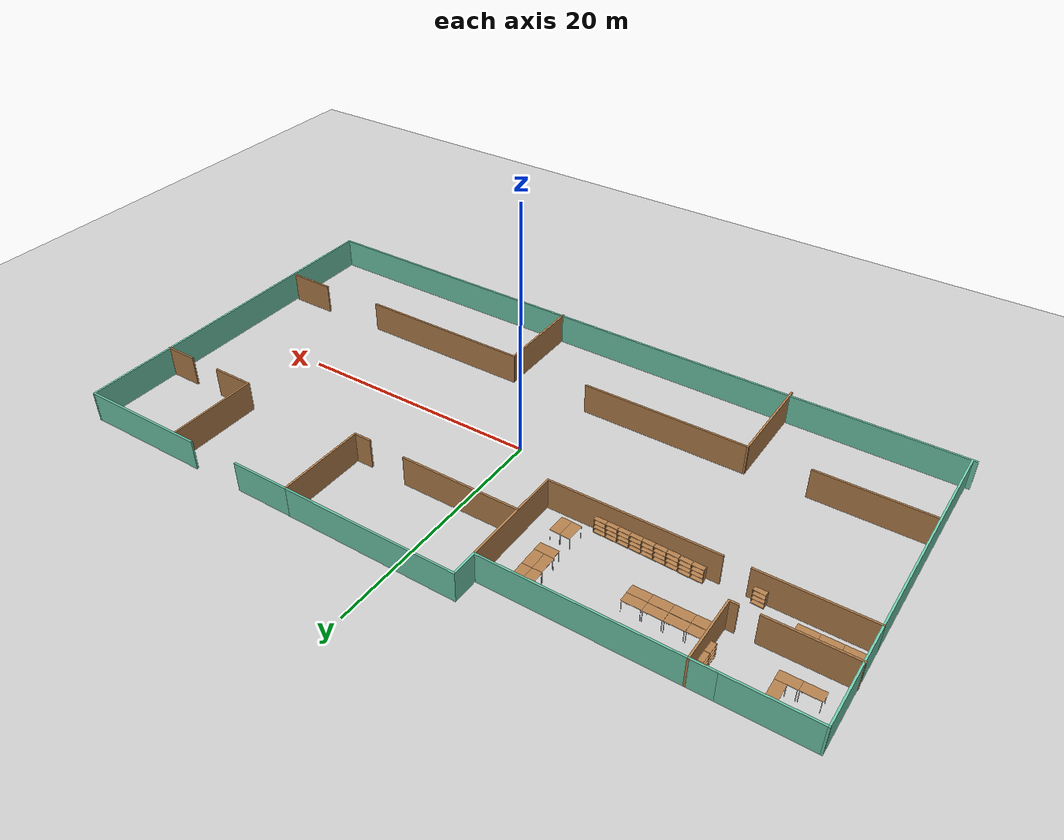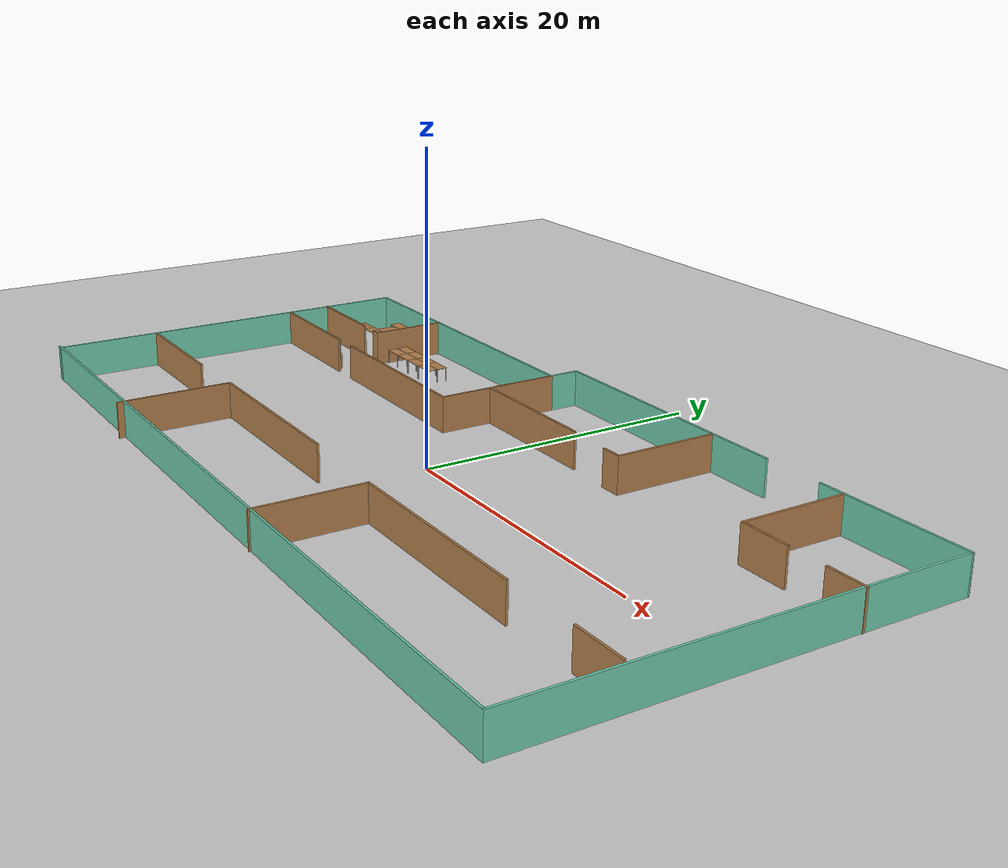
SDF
<sdf version="1.7">
 <world name="default">
  <light name="sun" type="directional">
   <pose>0 0 10 0 -0 0</pose>
   <diffuse>0.8 0.8 0.8 1</diffuse>
   <specular>0.2 0.2 0.2 1</specular>
   <attenuation>
    <range>1000</range>
    <constant>0.9</constant>
    <linear>0.01</linear>
    <quadratic>0.001</quadratic>
   </attenuation>
   <direction>-0.5 0.1 -0.9</direction>
   <spot><inner_angle>0</inner_angle><outer_angle>0</outer_angle><falloff>0</falloff></spot>
  </light>
  <model name="ground_plane">
   <static>1</static>
   <link name="link">
    <collision name="collision">
     <geometry><plane><normal>0 0 1</normal><size>100 100</size></plane></geometry>
     <surface>
      <contact><collide_bitmask>65535</collide_bitmask></contact>
      <friction><ode><mu>100</mu><mu2>50</mu2></ode></friction>
     </surface>
    </collision>
    <visual name="visual">
     <cast_shadows>0</cast_shadows>
     <geometry><plane><normal>0 0 1</normal><size>100 100</size></plane></geometry>
     <material>
      <script><uri>file://media/materials/scripts/gazebo.material</uri><name>Gazebo/Grey</name></script>
     </material>
    </visual>
   </link>
  </model>
  <gravity>0 0 -9.8</gravity>
  <magnetic_field>6e-06 2.3e-05 -4.2e-05</magnetic_field>
  <atmosphere type="adiabatic"/>
  <physics type="ode">
   <max_step_size>0.001</max_step_size>
   <real_time_factor>1</real_time_factor>
   <real_time_update_rate>1000</real_time_update_rate>
  </physics>
  <scene><ambient>0.4 0.4 0.4 1</ambient><background>0.7 0.7 0.7 1</background><shadows>1</shadows></scene>
  <spherical_coordinates>
   <surface_model>EARTH_WGS84</surface_model>
   <latitude_deg>0</latitude_deg>
   <longitude_deg>0</longitude_deg>
   <elevation>0</elevation>
   <heading_deg>0</heading_deg>
  </spherical_coordinates>
  <model name="full_office">
   <pose>0.0274 0.1655 0 0 -0 0</pose>
   <link name="Wall_0">
    <collision name="Wall_0_Collision">
     <geometry><box><size>17 0.15 2.5</size></box></geometry>
     <pose>0 0 1.25 0 -0 0</pose>
    </collision>
    <visual name="Wall_0_Visual">
     <pose>0 0 1.25 0 -0 0</pose>
     <geometry><box><size>17 0.15 2.5</size></box></geometry>
     <material>
      <script><uri>file://media/materials/scripts/gazebo.material</uri><name>Gazebo/Grey</name></script>
      <ambient>0.435294 0.796078 0.67451 1</ambient>
     </material>
     <meta><layer>0</layer></meta>
    </visual>
    <pose>-13.4599 12.605 0 0 -0 0</pose>
   </link>
   <link name="Wall_1">
    <collision name="Wall_1_Collision">
     <geometry><box><size>8.75 0.15 2.5</size></box></geometry>
     <pose>0 0 1.25 0 -0 0</pose>
    </collision>
    <visual name="Wall_1_Visual">
     <pose>0 0 1.25 0 -0 0</pose>
     <geometry><box><size>8.75 0.15 2.5</size></box></geometry>
     <material>
      <script><uri>file://media/materials/scripts/gazebo.material</uri><name>Gazebo/Wood</name></script>
      <ambient>1 0.764706 0.305882 1</ambient>
     </material>
     <meta><layer>0</layer></meta>
    </visual>
    <pose>-5.03487 8.30505 0 0 -0 -1.5708</pose>
   </link>
   <link name="Wall_12">
    <collision name="Wall_12_Collision">
     <geometry><box><size>6.5 0.15 2.5</size></box></geometry>
     <pose>0 0 1.25 0 -0 0</pose>
    </collision>
    <visual name="Wall_12_Visual">
     <pose>0 0 1.25 0 -0 0</pose>
     <geometry><box><size>6.5 0.15 2.5</size></box></geometry>
     <material>
      <script><uri>file://media/materials/scripts/gazebo.material</uri><name>Gazebo/Wood</name></script>
      <ambient>1 0.764706 0.305882 1</ambient>
     </material>
     <meta><layer>0</layer></meta>
    </visual>
    <pose>-25.359 7.2693 0 0 -0 0</pose>
   </link>
   <link name="Wall_14">
    <collision name="Wall_14_Collision">
     <geometry><box><size>0.75 0.15 2.5</size></box></geometry>
     <pose>0 0 1.25 0 -0 0</pose>
    </collision>
    <visual name="Wall_14_Visual">
     <pose>0 0 1.25 0 -0 0</pose>
     <geometry><box><size>0.75 0.15 2.5</size></box></geometry>
     <material>
      <script><uri>file://media/materials/scripts/gazebo.material</uri><name>Gazebo/Wood</name></script>
      <ambient>1 0.764706 0.305882 1</ambient>
     </material>
     <meta><layer>0</layer></meta>
    </visual>
    <pose>-20.387 7.2693 0 0 -0 0</pose>
   </link>
   <link name="Wall_15">
    <collision name="Wall_15_Collision">
     <geometry><box><size>5.5 0.15 2.5</size></box></geometry>
     <pose>0 0 1.25 0 -0 0</pose>
    </collision>
    <visual name="Wall_15_Visual">
     <pose>0 0 1.25 0 -0 0</pose>
     <geometry><box><size>5.5 0.15 2.5</size></box></geometry>
     <material>
      <script><uri>file://media/materials/scripts/gazebo.material</uri><name>Gazebo/Wood</name></script>
      <ambient>1 0.764706 0.305882 1</ambient>
     </material>
     <meta><layer>0</layer></meta>
    </visual>
    <pose>-20.087 9.9443 0 0 -0 1.5708</pose>
   </link>
   <link name="Wall_2">
    <collision name="Wall_2_Collision">
     <geometry><box><size>13.25 0.15 2.5</size></box></geometry>
     <pose>0 0 1.25 0 -0 0</pose>
    </collision>
    <visual name="Wall_2_Visual">
     <pose>0 0 1.25 0 -0 0</pose>
     <geometry><box><size>13.25 0.15 2.5</size></box></geometry>
     <material>
      <script><uri>file://media/materials/scripts/gazebo.material</uri><name>Gazebo/Wood</name></script>
      <ambient>1 0.764706 0.305882 1</ambient>
     </material>
     <meta><layer>0</layer></meta>
    </visual>
    <pose>-11.5849 4.00505 0 0 -0 3.14159</pose>
   </link>
   <link name="Wall_27">
    <collision name="Wall_27_Collision">
     <geometry><box><size>57.75 0.15 2.5</size></box></geometry>
     <pose>0 0 1.25 0 -0 0</pose>
    </collision>
    <visual name="Wall_27_Visual">
     <pose>0 0 1.25 0 -0 0</pose>
     <geometry><box><size>57.75 0.15 2.5</size></box></geometry>
     <material>
      <script><uri>file://media/materials/scripts/gazebo.material</uri><name>Gazebo/Grey</name></script>
      <ambient>0.435294 0.796078 0.67451 1</ambient>
     </material>
     <meta><layer>0</layer></meta>
    </visual>
    <pose>-0.020816 -14.3292 0 0 -0 0</pose>
   </link>
   <link name="Wall_28">
    <collision name="Wall_28_Collision">
     <geometry><box><size>29.25 0.15 2.5</size></box></geometry>
     <pose>0 0 1.25 0 -0 0</pose>
    </collision>
    <visual name="Wall_28_Visual">
     <pose>0 0 1.25 0 -0 0</pose>
     <geometry><box><size>29.25 0.15 2.5</size></box></geometry>
     <material>
      <script><uri>file://media/materials/scripts/gazebo.material</uri><name>Gazebo/Grey</name></script>
      <ambient>0.435294 0.796078 0.67451 1</ambient>
     </material>
     <meta><layer>0</layer></meta>
    </visual>
    <pose>28.7792 0.220838 0 0 -0 1.5708</pose>
   </link>
   <link name="Wall_32">
    <collision name="Wall_32_Collision">
     <geometry><box><size>2.25 0.15 2.5</size></box></geometry>
     <pose>0 0 1.25 0 -0 0</pose>
    </collision>
    <visual name="Wall_32_Visual">
     <pose>0 0 1.25 0 -0 0</pose>
     <geometry><box><size>2.25 0.15 2.5</size></box></geometry>
     <material>
      <script><uri>file://media/materials/scripts/gazebo.material</uri><name>Gazebo/Grey</name></script>
      <ambient>0.435294 0.796078 0.67451 1</ambient>
     </material>
     <meta><layer>0</layer></meta>
    </visual>
    <pose>-5.03487 13.655 0 0 -0 1.5708</pose>
   </link>
   <link name="Wall_37">
    <collision name="Wall_37_Collision">
     <geometry><box><size>9.75 0.15 2.5</size></box></geometry>
     <pose>0 0 1.25 0 -0 0</pose>
    </collision>
    <visual name="Wall_37_Visual">
     <pose>0 0 1.25 0 -0 0</pose>
     <geometry><box><size>9.75 0.15 2.5</size></box></geometry>
     <material>
      <script><uri>file://media/materials/scripts/gazebo.material</uri><name>Gazebo/Wood</name></script>
      <ambient>1 1 1 1</ambient>
     </material>
     <meta><layer>0</layer></meta>
    </visual>
    <pose>-0.207313 7.6604 0 0 -0 0</pose>
   </link>
   <link name="Wall_39">
    <collision name="Wall_39_Collision">
     <geometry><box><size>1.5 0.15 2.5</size></box></geometry>
     <pose>0 0 1.25 0 -0 0</pose>
    </collision>
    <visual name="Wall_39_Visual">
     <pose>0 0 1.25 0 -0 0</pose>
     <geometry><box><size>1.5 0.15 2.5</size></box></geometry>
     <material>
      <script><uri>file://media/materials/scripts/gazebo.material</uri><name>Gazebo/Wood</name></script>
      <ambient>1 1 1 1</ambient>
     </material>
     <meta><layer>0</layer></meta>
    </visual>
    <pose>8.53256 7.49858 0 0 -0 0</pose>
   </link>
   <link name="Wall_4">
    <collision name="Wall_4_Collision">
     <geometry><box><size>6.75 0.15 2.5</size></box></geometry>
     <pose>0 0 1.25 0 -0 0</pose>
    </collision>
    <visual name="Wall_4_Visual">
     <pose>0 0 1.25 0 -0 0</pose>
     <geometry><box><size>6.75 0.15 2.5</size></box></geometry>
     <material>
      <script><uri>file://media/materials/scripts/gazebo.material</uri><name>Gazebo/Grey</name></script>
      <ambient>0.435294 0.796078 0.67451 1</ambient>
     </material>
     <meta><layer>0</layer></meta>
    </visual>
    <pose>-25.1849 12.605 0 0 -0 3.14159</pose>
   </link>
   <link name="Wall_40">
    <collision name="Wall_40_Collision">
     <geometry><box><size>7.25 0.15 2.5</size></box></geometry>
     <pose>0 0 1.25 0 -0 0</pose>
    </collision>
    <visual name="Wall_40_Visual">
     <pose>0 0 1.25 0 -0 0</pose>
     <geometry><box><size>7.25 0.15 2.5</size></box></geometry>
     <material>
      <script><uri>file://media/materials/scripts/gazebo.material</uri><name>Gazebo/Wood</name></script>
      <ambient>1 1 1 1</ambient>
     </material>
     <meta><layer>0</layer></meta>
    </visual>
    <pose>9.20756 11.0486 0 0 -0 1.5708</pose>
   </link>
   <link name="Wall_42">
    <collision name="Wall_42_Collision">
     <geometry><box><size>7.5 0.15 2.5</size></box></geometry>
     <pose>0 0 1.25 0 -0 0</pose>
    </collision>
    <visual name="Wall_42_Visual">
     <pose>0 0 1.25 0 -0 0</pose>
     <geometry><box><size>7.5 0.15 2.5</size></box></geometry>
     <material>
      <script><uri>file://media/materials/scripts/gazebo.material</uri><name>Gazebo/Wood</name></script>
      <ambient>1 1 1 1</ambient>
     </material>
     <meta><layer>0</layer></meta>
    </visual>
    <pose>20.0751 11.0247 0 0 -0 -1.5708</pose>
   </link>
   <link name="Wall_43">
    <collision name="Wall_43_Collision">
     <geometry><box><size>3.5 0.15 2.5</size></box></geometry>
     <pose>0 0 1.25 0 -0 0</pose>
    </collision>
    <visual name="Wall_43_Visual">
     <pose>0 0 1.25 0 -0 0</pose>
     <geometry><box><size>3.5 0.15 2.5</size></box></geometry>
     <material>
      <script><uri>file://media/materials/scripts/gazebo.material</uri><name>Gazebo/Wood</name></script>
      <ambient>1 1 1 1</ambient>
     </material>
     <meta><layer>0</layer></meta>
    </visual>
    <pose>21.7501 7.34967 0 0 -0 0</pose>
   </link>
   <link name="Wall_45">
    <collision name="Wall_45_Collision">
     <geometry><box><size>2.75 0.15 2.5</size></box></geometry>
     <pose>0 0 1.25 0 -0 0</pose>
    </collision>
    <visual name="Wall_45_Visual">
     <pose>0 0 1.25 0 -0 0</pose>
     <geometry><box><size>2.75 0.15 2.5</size></box></geometry>
     <material>
      <script><uri>file://media/materials/scripts/gazebo.material</uri><name>Gazebo/Wood</name></script>
      <ambient>1 1 1 1</ambient>
     </material>
     <meta><layer>0</layer></meta>
    </visual>
    <pose>27.5208 7.33676 0 0 -0 3.14159</pose>
   </link>
   <link name="Wall_48">
    <collision name="Wall_48_Collision">
     <geometry><box><size>18.5 0.15 2.5</size></box></geometry>
     <pose>0 0 1.25 0 -0 0</pose>
    </collision>
    <visual name="Wall_48_Visual">
     <pose>0 0 1.25 0 -0 0</pose>
     <geometry><box><size>18.5 0.15 2.5</size></box></geometry>
     <material>
      <script><uri>file://media/materials/scripts/gazebo.material</uri><name>Gazebo/Grey</name></script>
      <ambient>0.435294 0.796078 0.67451 1</ambient>
     </material>
     <meta><layer>0</layer></meta>
    </visual>
    <pose>-28.4849 -5.16995 0 0 -0 -1.5708</pose>
   </link>
   <link name="Wall_5">
    <collision name="Wall_5_Collision">
     <geometry><box><size>8.75 0.15 2.5</size></box></geometry>
     <pose>0 0 1.25 0 -0 0</pose>
    </collision>
    <visual name="Wall_5_Visual">
     <pose>0 0 1.25 0 -0 0</pose>
     <geometry><box><size>8.75 0.15 2.5</size></box></geometry>
     <material>
      <script><uri>file://media/materials/scripts/gazebo.material</uri><name>Gazebo/Grey</name></script>
      <ambient>0.435294 0.796078 0.67451 1</ambient>
     </material>
     <meta><layer>0</layer></meta>
    </visual>
    <pose>-28.4849 8.30505 0 0 -0 -1.5708</pose>
   </link>
   <link name="Wall_50">
    <collision name="Wall_50_Collision">
     <geometry><box><size>9 0.15 2.5</size></box></geometry>
     <pose>0 0 1.25 0 -0 0</pose>
    </collision>
    <visual name="Wall_50_Visual">
     <pose>0 0 1.25 0 -0 0</pose>
     <geometry><box><size>9 0.15 2.5</size></box></geometry>
     <material>
      <script><uri>file://media/materials/scripts/gazebo.material</uri><name>Gazebo/Wood</name></script>
      <ambient>1 1 1 1</ambient>
     </material>
     <meta><layer>0</layer></meta>
    </visual>
    <pose>-24.0351 -7.08379 0 0 -0 0</pose>
   </link>
   <link name="Wall_52">
    <collision name="Wall_52_Collision">
     <geometry><box><size>13.5 0.15 2.5</size></box></geometry>
     <pose>0 0 1.25 0 -0 0</pose>
    </collision>
    <visual name="Wall_52_Visual">
     <pose>0 0 1.25 0 -0 0</pose>
     <geometry><box><size>13.5 0.15 2.5</size></box></geometry>
     <material>
      <script><uri>file://media/materials/scripts/gazebo.material</uri><name>Gazebo/Wood</name></script>
      <ambient>1 1 1 1</ambient>
     </material>
     <meta><layer>0</layer></meta>
    </visual>
    <pose>-8.1903 -6.92105 0 0 -0 0</pose>
   </link>
   <link name="Wall_54">
    <collision name="Wall_54_Collision">
     <geometry><box><size>14.25 0.15 2.5</size></box></geometry>
     <pose>0 0 1.25 0 -0 0</pose>
    </collision>
    <visual name="Wall_54_Visual">
     <pose>0 0 1.25 0 -0 0</pose>
     <geometry><box><size>14.25 0.15 2.5</size></box></geometry>
     <material>
      <script><uri>file://media/materials/scripts/gazebo.material</uri><name>Gazebo/Wood</name></script>
      <ambient>1 1 1 1</ambient>
     </material>
     <meta><layer>0</layer></meta>
    </visual>
    <pose>12.3646 -7.08379 0 0 -0 0</pose>
   </link>
   <link name="Wall_56">
    <collision name="Wall_56_Collision">
     <geometry><box><size>3.75 0.15 2.5</size></box></geometry>
     <pose>0 0 1.25 0 -0 0</pose>
    </collision>
    <visual name="Wall_56_Visual">
     <pose>0 0 1.25 0 -0 0</pose>
     <geometry><box><size>3.75 0.15 2.5</size></box></geometry>
     <material>
      <script><uri>file://media/materials/scripts/gazebo.material</uri><name>Gazebo/Wood</name></script>
      <ambient>1 1 1 1</ambient>
     </material>
     <meta><layer>0</layer></meta>
    </visual>
    <pose>26.6436 -6.92105 0 0 -0 0</pose>
   </link>
   <link name="Wall_58">
    <collision name="Wall_58_Collision">
     <geometry><box><size>8 0.15 2.5</size></box></geometry>
     <pose>0 0 1.25 0 -0 0</pose>
    </collision>
    <visual name="Wall_58_Visual">
     <pose>0 0 1.25 0 -0 0</pose>
     <geometry><box><size>8 0.15 2.5</size></box></geometry>
     <material>
      <script><uri>file://media/materials/scripts/gazebo.material</uri><name>Gazebo/Wood</name></script>
      <ambient>1 1 1 1</ambient>
     </material>
     <meta><layer>0</layer></meta>
    </visual>
    <pose>-14.8653 -10.846 0 0 -0 -1.5708</pose>
   </link>
   <link name="Wall_6">
    <collision name="Wall_6_Collision">
     <geometry><box><size>8.5 0.15 2.5</size></box></geometry>
     <pose>0 0 1.25 0 -0 0</pose>
    </collision>
    <visual name="Wall_6_Visual">
     <pose>0 0 1.25 0 -0 0</pose>
     <geometry><box><size>8.5 0.15 2.5</size></box></geometry>
     <material>
      <script><uri>file://media/materials/scripts/gazebo.material</uri><name>Gazebo/Wood</name></script>
      <ambient>1 0.764706 0.305882 1</ambient>
     </material>
     <meta><layer>0</layer></meta>
    </visual>
    <pose>-24.3099 4.00505 0 0 -0 0</pose>
   </link>
   <link name="Wall_62">
    <collision name="Wall_62_Collision">
     <geometry><box><size>7.5 0.15 2.5</size></box></geometry>
     <pose>0 0 1.25 0 -0 0</pose>
    </collision>
    <visual name="Wall_62_Visual">
     <pose>0 0 1.25 0 -0 0</pose>
     <geometry><box><size>7.5 0.15 2.5</size></box></geometry>
     <material>
      <script><uri>file://media/materials/scripts/gazebo.material</uri><name>Gazebo/Wood</name></script>
      <ambient>1 1 1 1</ambient>
     </material>
     <meta><layer>0</layer></meta>
    </visual>
    <pose>5.31461 -10.7588 0 0 -0 -1.5708</pose>
   </link>
   <link name="Wall_64">
    <collision name="Wall_64_Collision">
     <geometry><box><size>14.25 0.15 2.5</size></box></geometry>
     <pose>0 0 1.25 0 -0 0</pose>
    </collision>
    <visual name="Wall_64_Visual">
     <pose>0 0 1.25 0 -0 0</pose>
     <geometry><box><size>14.25 0.15 2.5</size></box></geometry>
     <material>
      <script><uri>file://media/materials/scripts/gazebo.material</uri><name>Gazebo/Grey</name></script>
      <ambient>0.435294 0.796078 0.67451 1</ambient>
     </material>
     <meta><layer>0</layer></meta>
    </visual>
    <pose>2.01513 14.705 0 0 -0 0</pose>
   </link>
   <link name="Wall_66">
    <collision name="Wall_66_Collision">
     <geometry><box><size>5 0.15 2.5</size></box></geometry>
     <pose>0 0 1.25 0 -0 0</pose>
    </collision>
    <visual name="Wall_66_Visual">
     <pose>0 0 1.25 0 -0 0</pose>
     <geometry><box><size>5 0.15 2.5</size></box></geometry>
     <material>
      <script><uri>file://media/materials/scripts/gazebo.material</uri><name>Gazebo/Grey</name></script>
      <ambient>0.435294 0.796078 0.67451 1</ambient>
     </material>
     <meta><layer>0</layer></meta>
    </visual>
    <pose>11.4901 14.705 0 0 -0 0</pose>
   </link>
   <link name="Wall_68">
    <collision name="Wall_68_Collision">
     <geometry><box><size>10.6315 0.15 2.5</size></box></geometry>
     <pose>0 0 1.25 0 -0 0</pose>
    </collision>
    <visual name="Wall_68_Visual">
     <pose>0 0 1.25 0 -0 0</pose>
     <geometry><box><size>10.6315 0.15 2.5</size></box></geometry>
     <material>
      <script><uri>file://media/materials/scripts/gazebo.material</uri><name>Gazebo/Grey</name></script>
      <ambient>0.435294 0.796078 0.67451 1</ambient>
     </material>
     <meta><layer>0</layer></meta>
    </visual>
    <pose>23.5385 14.756 0 0 -0 0.002825</pose>
   </link>
   <static>1</static>
  </model>
  <model name="table">
   <static>1</static>
   <link name="link">
    <collision name="surface">
     <pose>0 0 1 0 -0 0</pose>
     <geometry><box><size>1.5 0.8 0.03</size></box></geometry>
     <surface><friction><ode><mu>0.6</mu><mu2>0.6</mu2></ode></friction></surface>
    </collision>
    <visual name="visual1">
     <pose>0 0 1 0 -0 0</pose>
     <geometry><box><size>1.5 0.8 0.03</size></box></geometry>
     <material>
      <script><uri>file://media/materials/scripts/gazebo.material</uri><name>Gazebo/Wood</name></script>
     </material>
    </visual>
    <collision name="front_left_leg">
     <pose>0.68 0.38 0.5 0 -0 0</pose>
     <geometry><cylinder><radius>0.02</radius><length>1</length></cylinder></geometry>
    </collision>
    <visual name="front_left_leg">
     <pose>0.68 0.38 0.5 0 -0 0</pose>
     <geometry><cylinder><radius>0.02</radius><length>1</length></cylinder></geometry>
     <material>
      <script><uri>file://media/materials/scripts/gazebo.material</uri><name>Gazebo/Grey</name></script>
     </material>
    </visual>
    <collision name="front_right_leg">
     <pose>0.68 -0.38 0.5 0 -0 0</pose>
     <geometry><cylinder><radius>0.02</radius><length>1</length></cylinder></geometry>
    </collision>
    <visual name="front_right_leg">
     <pose>0.68 -0.38 0.5 0 -0 0</pose>
     <geometry><cylinder><radius>0.02</radius><length>1</length></cylinder></geometry>
     <material>
      <script><uri>file://media/materials/scripts/gazebo.material</uri><name>Gazebo/Grey</name></script>
     </material>
    </visual>
    <collision name="back_right_leg">
     <pose>-0.68 -0.38 0.5 0 -0 0</pose>
     <geometry><cylinder><radius>0.02</radius><length>1</length></cylinder></geometry>
    </collision>
    <visual name="back_right_leg">
     <pose>-0.68 -0.38 0.5 0 -0 0</pose>
     <geometry><cylinder><radius>0.02</radius><length>1</length></cylinder></geometry>
     <material>
      <script><uri>file://media/materials/scripts/gazebo.material</uri><name>Gazebo/Grey</name></script>
     </material>
    </visual>
    <collision name="back_left_leg">
     <pose>-0.68 0.38 0.5 0 -0 0</pose>
     <geometry><cylinder><radius>0.02</radius><length>1</length></cylinder></geometry>
    </collision>
    <visual name="back_left_leg">
     <pose>-0.68 0.38 0.5 0 -0 0</pose>
     <geometry><cylinder><radius>0.02</radius><length>1</length></cylinder></geometry>
     <material>
      <script><uri>file://media/materials/scripts/gazebo.material</uri><name>Gazebo/Grey</name></script>
     </material>
    </visual>
   </link>
   <pose>-19.2474 8.66386 0 0 -0 0</pose>
  </model>
  <model name="table_0">
   <static>1</static>
   <link name="link">
    <collision name="surface">
     <pose>0 0 1 0 -0 0</pose>
     <geometry><box><size>1.5 0.8 0.03</size></box></geometry>
     <surface><friction><ode><mu>0.6</mu><mu2>0.6</mu2></ode></friction></surface>
    </collision>
    <visual name="visual1">
     <pose>0 0 1 0 -0 0</pose>
     <geometry><box><size>1.5 0.8 0.03</size></box></geometry>
     <material>
      <script><uri>file://media/materials/scripts/gazebo.material</uri><name>Gazebo/Wood</name></script>
     </material>
    </visual>
    <collision name="front_left_leg">
     <pose>0.68 0.38 0.5 0 -0 0</pose>
     <geometry><cylinder><radius>0.02</radius><length>1</length></cylinder></geometry>
    </collision>
    <visual name="front_left_leg">
     <pose>0.68 0.38 0.5 0 -0 0</pose>
     <geometry><cylinder><radius>0.02</radius><length>1</length></cylinder></geometry>
     <material>
      <script><uri>file://media/materials/scripts/gazebo.material</uri><name>Gazebo/Grey</name></script>
     </material>
    </visual>
    <collision name="front_right_leg">
     <pose>0.68 -0.38 0.5 0 -0 0</pose>
     <geometry><cylinder><radius>0.02</radius><length>1</length></cylinder></geometry>
    </collision>
    <visual name="front_right_leg">
     <pose>0.68 -0.38 0.5 0 -0 0</pose>
     <geometry><cylinder><radius>0.02</radius><length>1</length></cylinder></geometry>
     <material>
      <script><uri>file://media/materials/scripts/gazebo.material</uri><name>Gazebo/Grey</name></script>
     </material>
    </visual>
    <collision name="back_right_leg">
     <pose>-0.68 -0.38 0.5 0 -0 0</pose>
     <geometry><cylinder><radius>0.02</radius><length>1</length></cylinder></geometry>
    </collision>
    <visual name="back_right_leg">
     <pose>-0.68 -0.38 0.5 0 -0 0</pose>
     <geometry><cylinder><radius>0.02</radius><length>1</length></cylinder></geometry>
     <material>
      <script><uri>file://media/materials/scripts/gazebo.material</uri><name>Gazebo/Grey</name></script>
     </material>
    </visual>
    <collision name="back_left_leg">
     <pose>-0.68 0.38 0.5 0 -0 0</pose>
     <geometry><cylinder><radius>0.02</radius><length>1</length></cylinder></geometry>
    </collision>
    <visual name="back_left_leg">
     <pose>-0.68 0.38 0.5 0 -0 0</pose>
     <geometry><cylinder><radius>0.02</radius><length>1</length></cylinder></geometry>
     <material>
      <script><uri>file://media/materials/scripts/gazebo.material</uri><name>Gazebo/Grey</name></script>
     </material>
    </visual>
   </link>
   <pose>-19.2889 9.4847 -0.00083 0 -0 0</pose>
  </model>
  <model name="table_0_clone">
   <static>1</static>
   <link name="link">
    <collision name="surface">
     <pose>0 0 1 0 -0 0</pose>
     <geometry><box><size>1.5 0.8 0.03</size></box></geometry>
     <surface><friction><ode><mu>0.6</mu><mu2>0.6</mu2></ode></friction></surface>
    </collision>
    <visual name="visual1">
     <pose>0 0 1 0 -0 0</pose>
     <geometry><box><size>1.5 0.8 0.03</size></box></geometry>
     <material>
      <script><uri>file://media/materials/scripts/gazebo.material</uri><name>Gazebo/Wood</name></script>
     </material>
    </visual>
    <collision name="front_left_leg">
     <pose>0.68 0.38 0.5 0 -0 0</pose>
     <geometry><cylinder><radius>0.02</radius><length>1</length></cylinder></geometry>
    </collision>
    <visual name="front_left_leg">
     <pose>0.68 0.38 0.5 0 -0 0</pose>
     <geometry><cylinder><radius>0.02</radius><length>1</length></cylinder></geometry>
     <material>
      <script><uri>file://media/materials/scripts/gazebo.material</uri><name>Gazebo/Grey</name></script>
     </material>
    </visual>
    <collision name="front_right_leg">
     <pose>0.68 -0.38 0.5 0 -0 0</pose>
     <geometry><cylinder><radius>0.02</radius><length>1</length></cylinder></geometry>
    </collision>
    <visual name="front_right_leg">
     <pose>0.68 -0.38 0.5 0 -0 0</pose>
     <geometry><cylinder><radius>0.02</radius><length>1</length></cylinder></geometry>
     <material>
      <script><uri>file://media/materials/scripts/gazebo.material</uri><name>Gazebo/Grey</name></script>
     </material>
    </visual>
    <collision name="back_right_leg">
     <pose>-0.68 -0.38 0.5 0 -0 0</pose>
     <geometry><cylinder><radius>0.02</radius><length>1</length></cylinder></geometry>
    </collision>
    <visual name="back_right_leg">
     <pose>-0.68 -0.38 0.5 0 -0 0</pose>
     <geometry><cylinder><radius>0.02</radius><length>1</length></cylinder></geometry>
     <material>
      <script><uri>file://media/materials/scripts/gazebo.material</uri><name>Gazebo/Grey</name></script>
     </material>
    </visual>
    <collision name="back_left_leg">
     <pose>-0.68 0.38 0.5 0 -0 0</pose>
     <geometry><cylinder><radius>0.02</radius><length>1</length></cylinder></geometry>
    </collision>
    <visual name="back_left_leg">
     <pose>-0.68 0.38 0.5 0 -0 0</pose>
     <geometry><cylinder><radius>0.02</radius><length>1</length></cylinder></geometry>
     <material>
      <script><uri>file://media/materials/scripts/gazebo.material</uri><name>Gazebo/Grey</name></script>
     </material>
    </visual>
   </link>
   <pose>-16.2542 8.67444 0 0 -0 0</pose>
  </model>
  <model name="table_0_clone_0">
   <static>1</static>
   <link name="link">
    <collision name="surface">
     <pose>0 0 1 0 -0 0</pose>
     <geometry><box><size>1.5 0.8 0.03</size></box></geometry>
     <surface><friction><ode><mu>0.6</mu><mu2>0.6</mu2></ode></friction></surface>
    </collision>
    <visual name="visual1">
     <pose>0 0 1 0 -0 0</pose>
     <geometry><box><size>1.5 0.8 0.03</size></box></geometry>
     <material>
      <script><uri>file://media/materials/scripts/gazebo.material</uri><name>Gazebo/Wood</name></script>
     </material>
    </visual>
    <collision name="front_left_leg">
     <pose>0.68 0.38 0.5 0 -0 0</pose>
     <geometry><cylinder><radius>0.02</radius><length>1</length></cylinder></geometry>
    </collision>
    <visual name="front_left_leg">
     <pose>0.68 0.38 0.5 0 -0 0</pose>
     <geometry><cylinder><radius>0.02</radius><length>1</length></cylinder></geometry>
     <material>
      <script><uri>file://media/materials/scripts/gazebo.material</uri><name>Gazebo/Grey</name></script>
     </material>
    </visual>
    <collision name="front_right_leg">
     <pose>0.68 -0.38 0.5 0 -0 0</pose>
     <geometry><cylinder><radius>0.02</radius><length>1</length></cylinder></geometry>
    </collision>
    <visual name="front_right_leg">
     <pose>0.68 -0.38 0.5 0 -0 0</pose>
     <geometry><cylinder><radius>0.02</radius><length>1</length></cylinder></geometry>
     <material>
      <script><uri>file://media/materials/scripts/gazebo.material</uri><name>Gazebo/Grey</name></script>
     </material>
    </visual>
    <collision name="back_right_leg">
     <pose>-0.68 -0.38 0.5 0 -0 0</pose>
     <geometry><cylinder><radius>0.02</radius><length>1</length></cylinder></geometry>
    </collision>
    <visual name="back_right_leg">
     <pose>-0.68 -0.38 0.5 0 -0 0</pose>
     <geometry><cylinder><radius>0.02</radius><length>1</length></cylinder></geometry>
     <material>
      <script><uri>file://media/materials/scripts/gazebo.material</uri><name>Gazebo/Grey</name></script>
     </material>
    </visual>
    <collision name="back_left_leg">
     <pose>-0.68 0.38 0.5 0 -0 0</pose>
     <geometry><cylinder><radius>0.02</radius><length>1</length></cylinder></geometry>
    </collision>
    <visual name="back_left_leg">
     <pose>-0.68 0.38 0.5 0 -0 0</pose>
     <geometry><cylinder><radius>0.02</radius><length>1</length></cylinder></geometry>
     <material>
      <script><uri>file://media/materials/scripts/gazebo.material</uri><name>Gazebo/Grey</name></script>
     </material>
    </visual>
   </link>
   <pose>-17.7586 8.67438 0 0 -0 0</pose>
  </model>
  <model name="table_0_clone_1">
   <static>1</static>
   <link name="link">
    <collision name="surface">
     <pose>0 0 1 0 -0 0</pose>
     <geometry><box><size>1.5 0.8 0.03</size></box></geometry>
     <surface><friction><ode><mu>0.6</mu><mu2>0.6</mu2></ode></friction></surface>
    </collision>
    <visual name="visual1">
     <pose>0 0 1 0 -0 0</pose>
     <geometry><box><size>1.5 0.8 0.03</size></box></geometry>
     <material>
      <script><uri>file://media/materials/scripts/gazebo.material</uri><name>Gazebo/Wood</name></script>
     </material>
    </visual>
    <collision name="front_left_leg">
     <pose>0.68 0.38 0.5 0 -0 0</pose>
     <geometry><cylinder><radius>0.02</radius><length>1</length></cylinder></geometry>
    </collision>
    <visual name="front_left_leg">
     <pose>0.68 0.38 0.5 0 -0 0</pose>
     <geometry><cylinder><radius>0.02</radius><length>1</length></cylinder></geometry>
     <material>
      <script><uri>file://media/materials/scripts/gazebo.material</uri><name>Gazebo/Grey</name></script>
     </material>
    </visual>
    <collision name="front_right_leg">
     <pose>0.68 -0.38 0.5 0 -0 0</pose>
     <geometry><cylinder><radius>0.02</radius><length>1</length></cylinder></geometry>
    </collision>
    <visual name="front_right_leg">
     <pose>0.68 -0.38 0.5 0 -0 0</pose>
     <geometry><cylinder><radius>0.02</radius><length>1</length></cylinder></geometry>
     <material>
      <script><uri>file://media/materials/scripts/gazebo.material</uri><name>Gazebo/Grey</name></script>
     </material>
    </visual>
    <collision name="back_right_leg">
     <pose>-0.68 -0.38 0.5 0 -0 0</pose>
     <geometry><cylinder><radius>0.02</radius><length>1</length></cylinder></geometry>
    </collision>
    <visual name="back_right_leg">
     <pose>-0.68 -0.38 0.5 0 -0 0</pose>
     <geometry><cylinder><radius>0.02</radius><length>1</length></cylinder></geometry>
     <material>
      <script><uri>file://media/materials/scripts/gazebo.material</uri><name>Gazebo/Grey</name></script>
     </material>
    </visual>
    <collision name="back_left_leg">
     <pose>-0.68 0.38 0.5 0 -0 0</pose>
     <geometry><cylinder><radius>0.02</radius><length>1</length></cylinder></geometry>
    </collision>
    <visual name="back_left_leg">
     <pose>-0.68 0.38 0.5 0 -0 0</pose>
     <geometry><cylinder><radius>0.02</radius><length>1</length></cylinder></geometry>
     <material>
      <script><uri>file://media/materials/scripts/gazebo.material</uri><name>Gazebo/Grey</name></script>
     </material>
    </visual>
   </link>
   <pose>-16.277 9.48331 0 0 -0 0</pose>
  </model>
  <model name="table_0_clone_2">
   <static>1</static>
   <link name="link">
    <collision name="surface">
     <pose>0 0 1 0 -0 0</pose>
     <geometry><box><size>1.5 0.8 0.03</size></box></geometry>
     <surface><friction><ode><mu>0.6</mu><mu2>0.6</mu2></ode></friction></surface>
    </collision>
    <visual name="visual1">
     <pose>0 0 1 0 -0 0</pose>
     <geometry><box><size>1.5 0.8 0.03</size></box></geometry>
     <material>
      <script><uri>file://media/materials/scripts/gazebo.material</uri><name>Gazebo/Wood</name></script>
     </material>
    </visual>
    <collision name="front_left_leg">
     <pose>0.68 0.38 0.5 0 -0 0</pose>
     <geometry><cylinder><radius>0.02</radius><length>1</length></cylinder></geometry>
    </collision>
    <visual name="front_left_leg">
     <pose>0.68 0.38 0.5 0 -0 0</pose>
     <geometry><cylinder><radius>0.02</radius><length>1</length></cylinder></geometry>
     <material>
      <script><uri>file://media/materials/scripts/gazebo.material</uri><name>Gazebo/Grey</name></script>
     </material>
    </visual>
    <collision name="front_right_leg">
     <pose>0.68 -0.38 0.5 0 -0 0</pose>
     <geometry><cylinder><radius>0.02</radius><length>1</length></cylinder></geometry>
    </collision>
    <visual name="front_right_leg">
     <pose>0.68 -0.38 0.5 0 -0 0</pose>
     <geometry><cylinder><radius>0.02</radius><length>1</length></cylinder></geometry>
     <material>
      <script><uri>file://media/materials/scripts/gazebo.material</uri><name>Gazebo/Grey</name></script>
     </material>
    </visual>
    <collision name="back_right_leg">
     <pose>-0.68 -0.38 0.5 0 -0 0</pose>
     <geometry><cylinder><radius>0.02</radius><length>1</length></cylinder></geometry>
    </collision>
    <visual name="back_right_leg">
     <pose>-0.68 -0.38 0.5 0 -0 0</pose>
     <geometry><cylinder><radius>0.02</radius><length>1</length></cylinder></geometry>
     <material>
      <script><uri>file://media/materials/scripts/gazebo.material</uri><name>Gazebo/Grey</name></script>
     </material>
    </visual>
    <collision name="back_left_leg">
     <pose>-0.68 0.38 0.5 0 -0 0</pose>
     <geometry><cylinder><radius>0.02</radius><length>1</length></cylinder></geometry>
    </collision>
    <visual name="back_left_leg">
     <pose>-0.68 0.38 0.5 0 -0 0</pose>
     <geometry><cylinder><radius>0.02</radius><length>1</length></cylinder></geometry>
     <material>
      <script><uri>file://media/materials/scripts/gazebo.material</uri><name>Gazebo/Grey</name></script>
     </material>
    </visual>
   </link>
   <pose>-14.7794 9.45664 0 0 -0 0</pose>
  </model>
  <model name="table_0_clone_3">
   <static>1</static>
   <link name="link">
    <collision name="surface">
     <pose>0 0 1 0 -0 0</pose>
     <geometry><box><size>1.5 0.8 0.03</size></box></geometry>
     <surface><friction><ode><mu>0.6</mu><mu2>0.6</mu2></ode></friction></surface>
    </collision>
    <visual name="visual1">
     <pose>0 0 1 0 -0 0</pose>
     <geometry><box><size>1.5 0.8 0.03</size></box></geometry>
     <material>
      <script><uri>file://media/materials/scripts/gazebo.material</uri><name>Gazebo/Wood</name></script>
     </material>
    </visual>
    <collision name="front_left_leg">
     <pose>0.68 0.38 0.5 0 -0 0</pose>
     <geometry><cylinder><radius>0.02</radius><length>1</length></cylinder></geometry>
    </collision>
    <visual name="front_left_leg">
     <pose>0.68 0.38 0.5 0 -0 0</pose>
     <geometry><cylinder><radius>0.02</radius><length>1</length></cylinder></geometry>
     <material>
      <script><uri>file://media/materials/scripts/gazebo.material</uri><name>Gazebo/Grey</name></script>
     </material>
    </visual>
    <collision name="front_right_leg">
     <pose>0.68 -0.38 0.5 0 -0 0</pose>
     <geometry><cylinder><radius>0.02</radius><length>1</length></cylinder></geometry>
    </collision>
    <visual name="front_right_leg">
     <pose>0.68 -0.38 0.5 0 -0 0</pose>
     <geometry><cylinder><radius>0.02</radius><length>1</length></cylinder></geometry>
     <material>
      <script><uri>file://media/materials/scripts/gazebo.material</uri><name>Gazebo/Grey</name></script>
     </material>
    </visual>
    <collision name="back_right_leg">
     <pose>-0.68 -0.38 0.5 0 -0 0</pose>
     <geometry><cylinder><radius>0.02</radius><length>1</length></cylinder></geometry>
    </collision>
    <visual name="back_right_leg">
     <pose>-0.68 -0.38 0.5 0 -0 0</pose>
     <geometry><cylinder><radius>0.02</radius><length>1</length></cylinder></geometry>
     <material>
      <script><uri>file://media/materials/scripts/gazebo.material</uri><name>Gazebo/Grey</name></script>
     </material>
    </visual>
    <collision name="back_left_leg">
     <pose>-0.68 0.38 0.5 0 -0 0</pose>
     <geometry><cylinder><radius>0.02</radius><length>1</length></cylinder></geometry>
    </collision>
    <visual name="back_left_leg">
     <pose>-0.68 0.38 0.5 0 -0 0</pose>
     <geometry><cylinder><radius>0.02</radius><length>1</length></cylinder></geometry>
     <material>
      <script><uri>file://media/materials/scripts/gazebo.material</uri><name>Gazebo/Grey</name></script>
     </material>
    </visual>
   </link>
   <pose>-14.7658 8.68214 0 0 -0 0</pose>
  </model>
  <model name="table_0_clone_4">
   <static>1</static>
   <link name="link">
    <collision name="surface">
     <pose>0 0 1 0 -0 0</pose>
     <geometry><box><size>1.5 0.8 0.03</size></box></geometry>
     <surface><friction><ode><mu>0.6</mu><mu2>0.6</mu2></ode></friction></surface>
    </collision>
    <visual name="visual1">
     <pose>0 0 1 0 -0 0</pose>
     <geometry><box><size>1.5 0.8 0.03</size></box></geometry>
     <material>
      <script><uri>file://media/materials/scripts/gazebo.material</uri><name>Gazebo/Wood</name></script>
     </material>
    </visual>
    <collision name="front_left_leg">
     <pose>0.68 0.38 0.5 0 -0 0</pose>
     <geometry><cylinder><radius>0.02</radius><length>1</length></cylinder></geometry>
    </collision>
    <visual name="front_left_leg">
     <pose>0.68 0.38 0.5 0 -0 0</pose>
     <geometry><cylinder><radius>0.02</radius><length>1</length></cylinder></geometry>
     <material>
      <script><uri>file://media/materials/scripts/gazebo.material</uri><name>Gazebo/Grey</name></script>
     </material>
    </visual>
    <collision name="front_right_leg">
     <pose>0.68 -0.38 0.5 0 -0 0</pose>
     <geometry><cylinder><radius>0.02</radius><length>1</length></cylinder></geometry>
    </collision>
    <visual name="front_right_leg">
     <pose>0.68 -0.38 0.5 0 -0 0</pose>
     <geometry><cylinder><radius>0.02</radius><length>1</length></cylinder></geometry>
     <material>
      <script><uri>file://media/materials/scripts/gazebo.material</uri><name>Gazebo/Grey</name></script>
     </material>
    </visual>
    <collision name="back_right_leg">
     <pose>-0.68 -0.38 0.5 0 -0 0</pose>
     <geometry><cylinder><radius>0.02</radius><length>1</length></cylinder></geometry>
    </collision>
    <visual name="back_right_leg">
     <pose>-0.68 -0.38 0.5 0 -0 0</pose>
     <geometry><cylinder><radius>0.02</radius><length>1</length></cylinder></geometry>
     <material>
      <script><uri>file://media/materials/scripts/gazebo.material</uri><name>Gazebo/Grey</name></script>
     </material>
    </visual>
    <collision name="back_left_leg">
     <pose>-0.68 0.38 0.5 0 -0 0</pose>
     <geometry><cylinder><radius>0.02</radius><length>1</length></cylinder></geometry>
    </collision>
    <visual name="back_left_leg">
     <pose>-0.68 0.38 0.5 0 -0 0</pose>
     <geometry><cylinder><radius>0.02</radius><length>1</length></cylinder></geometry>
     <material>
      <script><uri>file://media/materials/scripts/gazebo.material</uri><name>Gazebo/Grey</name></script>
     </material>
    </visual>
   </link>
   <pose>-17.7882 9.49595 0 0 -0 0</pose>
  </model>
  <model name="table_0_clone_6">
   <static>1</static>
   <link name="link">
    <collision name="surface">
     <pose>0 0 1 0 -0 0</pose>
     <geometry><box><size>1.5 0.8 0.03</size></box></geometry>
     <surface><friction><ode><mu>0.6</mu><mu2>0.6</mu2></ode></friction></surface>
    </collision>
    <visual name="visual1">
     <pose>0 0 1 0 -0 0</pose>
     <geometry><box><size>1.5 0.8 0.03</size></box></geometry>
     <material>
      <script><uri>file://media/materials/scripts/gazebo.material</uri><name>Gazebo/Wood</name></script>
     </material>
    </visual>
    <collision name="front_left_leg">
     <pose>0.68 0.38 0.5 0 -0 0</pose>
     <geometry><cylinder><radius>0.02</radius><length>1</length></cylinder></geometry>
    </collision>
    <visual name="front_left_leg">
     <pose>0.68 0.38 0.5 0 -0 0</pose>
     <geometry><cylinder><radius>0.02</radius><length>1</length></cylinder></geometry>
     <material>
      <script><uri>file://media/materials/scripts/gazebo.material</uri><name>Gazebo/Grey</name></script>
     </material>
    </visual>
    <collision name="front_right_leg">
     <pose>0.68 -0.38 0.5 0 -0 0</pose>
     <geometry><cylinder><radius>0.02</radius><length>1</length></cylinder></geometry>
    </collision>
    <visual name="front_right_leg">
     <pose>0.68 -0.38 0.5 0 -0 0</pose>
     <geometry><cylinder><radius>0.02</radius><length>1</length></cylinder></geometry>
     <material>
      <script><uri>file://media/materials/scripts/gazebo.material</uri><name>Gazebo/Grey</name></script>
     </material>
    </visual>
    <collision name="back_right_leg">
     <pose>-0.68 -0.38 0.5 0 -0 0</pose>
     <geometry><cylinder><radius>0.02</radius><length>1</length></cylinder></geometry>
    </collision>
    <visual name="back_right_leg">
     <pose>-0.68 -0.38 0.5 0 -0 0</pose>
     <geometry><cylinder><radius>0.02</radius><length>1</length></cylinder></geometry>
     <material>
      <script><uri>file://media/materials/scripts/gazebo.material</uri><name>Gazebo/Grey</name></script>
     </material>
    </visual>
    <collision name="back_left_leg">
     <pose>-0.68 0.38 0.5 0 -0 0</pose>
     <geometry><cylinder><radius>0.02</radius><length>1</length></cylinder></geometry>
    </collision>
    <visual name="back_left_leg">
     <pose>-0.68 0.38 0.5 0 -0 0</pose>
     <geometry><cylinder><radius>0.02</radius><length>1</length></cylinder></geometry>
     <material>
      <script><uri>file://media/materials/scripts/gazebo.material</uri><name>Gazebo/Grey</name></script>
     </material>
    </visual>
   </link>
   <pose>-8.18867 6.22527 7.2e-05 0.000175 0.010072 1.53538</pose>
  </model>
  <model name="table_0_clone_7">
   <static>1</static>
   <link name="link">
    <collision name="surface">
     <pose>0 0 1 0 -0 0</pose>
     <geometry><box><size>1.5 0.8 0.03</size></box></geometry>
     <surface><friction><ode><mu>0.6</mu><mu2>0.6</mu2></ode></friction></surface>
    </collision>
    <visual name="visual1">
     <pose>0 0 1 0 -0 0</pose>
     <geometry><box><size>1.5 0.8 0.03</size></box></geometry>
     <material>
      <script><uri>file://media/materials/scripts/gazebo.material</uri><name>Gazebo/Wood</name></script>
     </material>
    </visual>
    <collision name="front_left_leg">
     <pose>0.68 0.38 0.5 0 -0 0</pose>
     <geometry><cylinder><radius>0.02</radius><length>1</length></cylinder></geometry>
    </collision>
    <visual name="front_left_leg">
     <pose>0.68 0.38 0.5 0 -0 0</pose>
     <geometry><cylinder><radius>0.02</radius><length>1</length></cylinder></geometry>
     <material>
      <script><uri>file://media/materials/scripts/gazebo.material</uri><name>Gazebo/Grey</name></script>
     </material>
    </visual>
    <collision name="front_right_leg">
     <pose>0.68 -0.38 0.5 0 -0 0</pose>
     <geometry><cylinder><radius>0.02</radius><length>1</length></cylinder></geometry>
    </collision>
    <visual name="front_right_leg">
     <pose>0.68 -0.38 0.5 0 -0 0</pose>
     <geometry><cylinder><radius>0.02</radius><length>1</length></cylinder></geometry>
     <material>
      <script><uri>file://media/materials/scripts/gazebo.material</uri><name>Gazebo/Grey</name></script>
     </material>
    </visual>
    <collision name="back_right_leg">
     <pose>-0.68 -0.38 0.5 0 -0 0</pose>
     <geometry><cylinder><radius>0.02</radius><length>1</length></cylinder></geometry>
    </collision>
    <visual name="back_right_leg">
     <pose>-0.68 -0.38 0.5 0 -0 0</pose>
     <geometry><cylinder><radius>0.02</radius><length>1</length></cylinder></geometry>
     <material>
      <script><uri>file://media/materials/scripts/gazebo.material</uri><name>Gazebo/Grey</name></script>
     </material>
    </visual>
    <collision name="back_left_leg">
     <pose>-0.68 0.38 0.5 0 -0 0</pose>
     <geometry><cylinder><radius>0.02</radius><length>1</length></cylinder></geometry>
    </collision>
    <visual name="back_left_leg">
     <pose>-0.68 0.38 0.5 0 -0 0</pose>
     <geometry><cylinder><radius>0.02</radius><length>1</length></cylinder></geometry>
     <material>
      <script><uri>file://media/materials/scripts/gazebo.material</uri><name>Gazebo/Grey</name></script>
     </material>
    </visual>
   </link>
   <pose>-7.38527 6.20263 0 0 0 -1.60113</pose>
  </model>
  <model name="table_1">
   <static>1</static>
   <link name="link">
    <collision name="surface">
     <pose>0 0 1 0 -0 0</pose>
     <geometry><box><size>1.5 0.8 0.03</size></box></geometry>
     <surface><friction><ode><mu>0.6</mu><mu2>0.6</mu2></ode></friction></surface>
    </collision>
    <visual name="visual1">
     <pose>0 0 1 0 -0 0</pose>
     <geometry><box><size>1.5 0.8 0.03</size></box></geometry>
     <material>
      <script><uri>file://media/materials/scripts/gazebo.material</uri><name>Gazebo/Wood</name></script>
     </material>
    </visual>
    <collision name="front_left_leg">
     <pose>0.68 0.38 0.5 0 -0 0</pose>
     <geometry><cylinder><radius>0.02</radius><length>1</length></cylinder></geometry>
    </collision>
    <visual name="front_left_leg">
     <pose>0.68 0.38 0.5 0 -0 0</pose>
     <geometry><cylinder><radius>0.02</radius><length>1</length></cylinder></geometry>
     <material>
      <script><uri>file://media/materials/scripts/gazebo.material</uri><name>Gazebo/Grey</name></script>
     </material>
    </visual>
    <collision name="front_right_leg">
     <pose>0.68 -0.38 0.5 0 -0 0</pose>
     <geometry><cylinder><radius>0.02</radius><length>1</length></cylinder></geometry>
    </collision>
    <visual name="front_right_leg">
     <pose>0.68 -0.38 0.5 0 -0 0</pose>
     <geometry><cylinder><radius>0.02</radius><length>1</length></cylinder></geometry>
     <material>
      <script><uri>file://media/materials/scripts/gazebo.material</uri><name>Gazebo/Grey</name></script>
     </material>
    </visual>
    <collision name="back_right_leg">
     <pose>-0.68 -0.38 0.5 0 -0 0</pose>
     <geometry><cylinder><radius>0.02</radius><length>1</length></cylinder></geometry>
    </collision>
    <visual name="back_right_leg">
     <pose>-0.68 -0.38 0.5 0 -0 0</pose>
     <geometry><cylinder><radius>0.02</radius><length>1</length></cylinder></geometry>
     <material>
      <script><uri>file://media/materials/scripts/gazebo.material</uri><name>Gazebo/Grey</name></script>
     </material>
    </visual>
    <collision name="back_left_leg">
     <pose>-0.68 0.38 0.5 0 -0 0</pose>
     <geometry><cylinder><radius>0.02</radius><length>1</length></cylinder></geometry>
    </collision>
    <visual name="back_left_leg">
     <pose>-0.68 0.38 0.5 0 -0 0</pose>
     <geometry><cylinder><radius>0.02</radius><length>1</length></cylinder></geometry>
     <material>
      <script><uri>file://media/materials/scripts/gazebo.material</uri><name>Gazebo/Grey</name></script>
     </material>
    </visual>
   </link>
   <pose>-7.56843 11.3268 0 0 0 -1.56551</pose>
  </model>
  <model name="table_1_clone">
   <static>1</static>
   <link name="link">
    <collision name="surface">
     <pose>0 0 1 0 -0 0</pose>
     <geometry><box><size>1.5 0.8 0.03</size></box></geometry>
     <surface><friction><ode><mu>0.6</mu><mu2>0.6</mu2></ode></friction></surface>
    </collision>
    <visual name="visual1">
     <pose>0 0 1 0 -0 0</pose>
     <geometry><box><size>1.5 0.8 0.03</size></box></geometry>
     <material>
      <script><uri>file://media/materials/scripts/gazebo.material</uri><name>Gazebo/Wood</name></script>
     </material>
    </visual>
    <collision name="front_left_leg">
     <pose>0.68 0.38 0.5 0 -0 0</pose>
     <geometry><cylinder><radius>0.02</radius><length>1</length></cylinder></geometry>
    </collision>
    <visual name="front_left_leg">
     <pose>0.68 0.38 0.5 0 -0 0</pose>
     <geometry><cylinder><radius>0.02</radius><length>1</length></cylinder></geometry>
     <material>
      <script><uri>file://media/materials/scripts/gazebo.material</uri><name>Gazebo/Grey</name></script>
     </material>
    </visual>
    <collision name="front_right_leg">
     <pose>0.68 -0.38 0.5 0 -0 0</pose>
     <geometry><cylinder><radius>0.02</radius><length>1</length></cylinder></geometry>
    </collision>
    <visual name="front_right_leg">
     <pose>0.68 -0.38 0.5 0 -0 0</pose>
     <geometry><cylinder><radius>0.02</radius><length>1</length></cylinder></geometry>
     <material>
      <script><uri>file://media/materials/scripts/gazebo.material</uri><name>Gazebo/Grey</name></script>
     </material>
    </visual>
    <collision name="back_right_leg">
     <pose>-0.68 -0.38 0.5 0 -0 0</pose>
     <geometry><cylinder><radius>0.02</radius><length>1</length></cylinder></geometry>
    </collision>
    <visual name="back_right_leg">
     <pose>-0.68 -0.38 0.5 0 -0 0</pose>
     <geometry><cylinder><radius>0.02</radius><length>1</length></cylinder></geometry>
     <material>
      <script><uri>file://media/materials/scripts/gazebo.material</uri><name>Gazebo/Grey</name></script>
     </material>
    </visual>
    <collision name="back_left_leg">
     <pose>-0.68 0.38 0.5 0 -0 0</pose>
     <geometry><cylinder><radius>0.02</radius><length>1</length></cylinder></geometry>
    </collision>
    <visual name="back_left_leg">
     <pose>-0.68 0.38 0.5 0 -0 0</pose>
     <geometry><cylinder><radius>0.02</radius><length>1</length></cylinder></geometry>
     <material>
      <script><uri>file://media/materials/scripts/gazebo.material</uri><name>Gazebo/Grey</name></script>
     </material>
    </visual>
   </link>
   <pose>-7.54764 9.82281 0 0 0 -1.56551</pose>
  </model>
  <model name="table_1_clone_0">
   <static>1</static>
   <link name="link">
    <collision name="surface">
     <pose>0 0 1 0 -0 0</pose>
     <geometry><box><size>1.5 0.8 0.03</size></box></geometry>
     <surface><friction><ode><mu>0.6</mu><mu2>0.6</mu2></ode></friction></surface>
    </collision>
    <visual name="visual1">
     <pose>0 0 1 0 -0 0</pose>
     <geometry><box><size>1.5 0.8 0.03</size></box></geometry>
     <material>
      <script><uri>file://media/materials/scripts/gazebo.material</uri><name>Gazebo/Wood</name></script>
     </material>
    </visual>
    <collision name="front_left_leg">
     <pose>0.68 0.38 0.5 0 -0 0</pose>
     <geometry><cylinder><radius>0.02</radius><length>1</length></cylinder></geometry>
    </collision>
    <visual name="front_left_leg">
     <pose>0.68 0.38 0.5 0 -0 0</pose>
     <geometry><cylinder><radius>0.02</radius><length>1</length></cylinder></geometry>
     <material>
      <script><uri>file://media/materials/scripts/gazebo.material</uri><name>Gazebo/Grey</name></script>
     </material>
    </visual>
    <collision name="front_right_leg">
     <pose>0.68 -0.38 0.5 0 -0 0</pose>
     <geometry><cylinder><radius>0.02</radius><length>1</length></cylinder></geometry>
    </collision>
    <visual name="front_right_leg">
     <pose>0.68 -0.38 0.5 0 -0 0</pose>
     <geometry><cylinder><radius>0.02</radius><length>1</length></cylinder></geometry>
     <material>
      <script><uri>file://media/materials/scripts/gazebo.material</uri><name>Gazebo/Grey</name></script>
     </material>
    </visual>
    <collision name="back_right_leg">
     <pose>-0.68 -0.38 0.5 0 -0 0</pose>
     <geometry><cylinder><radius>0.02</radius><length>1</length></cylinder></geometry>
    </collision>
    <visual name="back_right_leg">
     <pose>-0.68 -0.38 0.5 0 -0 0</pose>
     <geometry><cylinder><radius>0.02</radius><length>1</length></cylinder></geometry>
     <material>
      <script><uri>file://media/materials/scripts/gazebo.material</uri><name>Gazebo/Grey</name></script>
     </material>
    </visual>
    <collision name="back_left_leg">
     <pose>-0.68 0.38 0.5 0 -0 0</pose>
     <geometry><cylinder><radius>0.02</radius><length>1</length></cylinder></geometry>
    </collision>
    <visual name="back_left_leg">
     <pose>-0.68 0.38 0.5 0 -0 0</pose>
     <geometry><cylinder><radius>0.02</radius><length>1</length></cylinder></geometry>
     <material>
      <script><uri>file://media/materials/scripts/gazebo.material</uri><name>Gazebo/Grey</name></script>
     </material>
    </visual>
   </link>
   <pose>-8.35898 11.3174 0 0 0 -1.56551</pose>
  </model>
  <model name="table_1_clone_1">
   <static>1</static>
   <link name="link">
    <collision name="surface">
     <pose>0 0 1 0 -0 0</pose>
     <geometry><box><size>1.5 0.8 0.03</size></box></geometry>
     <surface><friction><ode><mu>0.6</mu><mu2>0.6</mu2></ode></friction></surface>
    </collision>
    <visual name="visual1">
     <pose>0 0 1 0 -0 0</pose>
     <geometry><box><size>1.5 0.8 0.03</size></box></geometry>
     <material>
      <script><uri>file://media/materials/scripts/gazebo.material</uri><name>Gazebo/Wood</name></script>
     </material>
    </visual>
    <collision name="front_left_leg">
     <pose>0.68 0.38 0.5 0 -0 0</pose>
     <geometry><cylinder><radius>0.02</radius><length>1</length></cylinder></geometry>
    </collision>
    <visual name="front_left_leg">
     <pose>0.68 0.38 0.5 0 -0 0</pose>
     <geometry><cylinder><radius>0.02</radius><length>1</length></cylinder></geometry>
     <material>
      <script><uri>file://media/materials/scripts/gazebo.material</uri><name>Gazebo/Grey</name></script>
     </material>
    </visual>
    <collision name="front_right_leg">
     <pose>0.68 -0.38 0.5 0 -0 0</pose>
     <geometry><cylinder><radius>0.02</radius><length>1</length></cylinder></geometry>
    </collision>
    <visual name="front_right_leg">
     <pose>0.68 -0.38 0.5 0 -0 0</pose>
     <geometry><cylinder><radius>0.02</radius><length>1</length></cylinder></geometry>
     <material>
      <script><uri>file://media/materials/scripts/gazebo.material</uri><name>Gazebo/Grey</name></script>
     </material>
    </visual>
    <collision name="back_right_leg">
     <pose>-0.68 -0.38 0.5 0 -0 0</pose>
     <geometry><cylinder><radius>0.02</radius><length>1</length></cylinder></geometry>
    </collision>
    <visual name="back_right_leg">
     <pose>-0.68 -0.38 0.5 0 -0 0</pose>
     <geometry><cylinder><radius>0.02</radius><length>1</length></cylinder></geometry>
     <material>
      <script><uri>file://media/materials/scripts/gazebo.material</uri><name>Gazebo/Grey</name></script>
     </material>
    </visual>
    <collision name="back_left_leg">
     <pose>-0.68 0.38 0.5 0 -0 0</pose>
     <geometry><cylinder><radius>0.02</radius><length>1</length></cylinder></geometry>
    </collision>
    <visual name="back_left_leg">
     <pose>-0.68 0.38 0.5 0 -0 0</pose>
     <geometry><cylinder><radius>0.02</radius><length>1</length></cylinder></geometry>
     <material>
      <script><uri>file://media/materials/scripts/gazebo.material</uri><name>Gazebo/Grey</name></script>
     </material>
    </visual>
   </link>
   <pose>-8.30936 9.82451 0 0 0 -1.56551</pose>
  </model>
  <model name="table_1_clone_2">
   <static>1</static>
   <link name="link">
    <collision name="surface">
     <pose>0 0 1 0 -0 0</pose>
     <geometry><box><size>1.5 0.8 0.03</size></box></geometry>
     <surface><friction><ode><mu>0.6</mu><mu2>0.6</mu2></ode></friction></surface>
    </collision>
    <visual name="visual1">
     <pose>0 0 1 0 -0 0</pose>
     <geometry><box><size>1.5 0.8 0.03</size></box></geometry>
     <material>
      <script><uri>file://media/materials/scripts/gazebo.material</uri><name>Gazebo/Wood</name></script>
     </material>
    </visual>
    <collision name="front_left_leg">
     <pose>0.68 0.38 0.5 0 -0 0</pose>
     <geometry><cylinder><radius>0.02</radius><length>1</length></cylinder></geometry>
    </collision>
    <visual name="front_left_leg">
     <pose>0.68 0.38 0.5 0 -0 0</pose>
     <geometry><cylinder><radius>0.02</radius><length>1</length></cylinder></geometry>
     <material>
      <script><uri>file://media/materials/scripts/gazebo.material</uri><name>Gazebo/Grey</name></script>
     </material>
    </visual>
    <collision name="front_right_leg">
     <pose>0.68 -0.38 0.5 0 -0 0</pose>
     <geometry><cylinder><radius>0.02</radius><length>1</length></cylinder></geometry>
    </collision>
    <visual name="front_right_leg">
     <pose>0.68 -0.38 0.5 0 -0 0</pose>
     <geometry><cylinder><radius>0.02</radius><length>1</length></cylinder></geometry>
     <material>
      <script><uri>file://media/materials/scripts/gazebo.material</uri><name>Gazebo/Grey</name></script>
     </material>
    </visual>
    <collision name="back_right_leg">
     <pose>-0.68 -0.38 0.5 0 -0 0</pose>
     <geometry><cylinder><radius>0.02</radius><length>1</length></cylinder></geometry>
    </collision>
    <visual name="back_right_leg">
     <pose>-0.68 -0.38 0.5 0 -0 0</pose>
     <geometry><cylinder><radius>0.02</radius><length>1</length></cylinder></geometry>
     <material>
      <script><uri>file://media/materials/scripts/gazebo.material</uri><name>Gazebo/Grey</name></script>
     </material>
    </visual>
    <collision name="back_left_leg">
     <pose>-0.68 0.38 0.5 0 -0 0</pose>
     <geometry><cylinder><radius>0.02</radius><length>1</length></cylinder></geometry>
    </collision>
    <visual name="back_left_leg">
     <pose>-0.68 0.38 0.5 0 -0 0</pose>
     <geometry><cylinder><radius>0.02</radius><length>1</length></cylinder></geometry>
     <material>
      <script><uri>file://media/materials/scripts/gazebo.material</uri><name>Gazebo/Grey</name></script>
     </material>
    </visual>
   </link>
   <pose>-7.88545 8.70408 0 0 0 -0.008076</pose>
  </model>
  <model name="table_2">
   <static>1</static>
   <link name="link">
    <collision name="surface">
     <pose>0 0 1 0 -0 0</pose>
     <geometry><box><size>1.5 0.8 0.03</size></box></geometry>
     <surface><friction><ode><mu>0.6</mu><mu2>0.6</mu2></ode></friction></surface>
    </collision>
    <visual name="visual1">
     <pose>0 0 1 0 -0 0</pose>
     <geometry><box><size>1.5 0.8 0.03</size></box></geometry>
     <material>
      <script><uri>file://media/materials/scripts/gazebo.material</uri><name>Gazebo/Wood</name></script>
     </material>
    </visual>
    <collision name="front_left_leg">
     <pose>0.68 0.38 0.5 0 -0 0</pose>
     <geometry><cylinder><radius>0.02</radius><length>1</length></cylinder></geometry>
    </collision>
    <visual name="front_left_leg">
     <pose>0.68 0.38 0.5 0 -0 0</pose>
     <geometry><cylinder><radius>0.02</radius><length>1</length></cylinder></geometry>
     <material>
      <script><uri>file://media/materials/scripts/gazebo.material</uri><name>Gazebo/Grey</name></script>
     </material>
    </visual>
    <collision name="front_right_leg">
     <pose>0.68 -0.38 0.5 0 -0 0</pose>
     <geometry><cylinder><radius>0.02</radius><length>1</length></cylinder></geometry>
    </collision>
    <visual name="front_right_leg">
     <pose>0.68 -0.38 0.5 0 -0 0</pose>
     <geometry><cylinder><radius>0.02</radius><length>1</length></cylinder></geometry>
     <material>
      <script><uri>file://media/materials/scripts/gazebo.material</uri><name>Gazebo/Grey</name></script>
     </material>
    </visual>
    <collision name="back_right_leg">
     <pose>-0.68 -0.38 0.5 0 -0 0</pose>
     <geometry><cylinder><radius>0.02</radius><length>1</length></cylinder></geometry>
    </collision>
    <visual name="back_right_leg">
     <pose>-0.68 -0.38 0.5 0 -0 0</pose>
     <geometry><cylinder><radius>0.02</radius><length>1</length></cylinder></geometry>
     <material>
      <script><uri>file://media/materials/scripts/gazebo.material</uri><name>Gazebo/Grey</name></script>
     </material>
    </visual>
    <collision name="back_left_leg">
     <pose>-0.68 0.38 0.5 0 -0 0</pose>
     <geometry><cylinder><radius>0.02</radius><length>1</length></cylinder></geometry>
    </collision>
    <visual name="back_left_leg">
     <pose>-0.68 0.38 0.5 0 -0 0</pose>
     <geometry><cylinder><radius>0.02</radius><length>1</length></cylinder></geometry>
     <material>
      <script><uri>file://media/materials/scripts/gazebo.material</uri><name>Gazebo/Grey</name></script>
     </material>
    </visual>
   </link>
   <pose>-26.6345 9.80298 0 0 -0 0</pose>
  </model>
  <model name="table_2_clone">
   <static>1</static>
   <link name="link">
    <collision name="surface">
     <pose>0 0 1 0 -0 0</pose>
     <geometry><box><size>1.5 0.8 0.03</size></box></geometry>
     <surface><friction><ode><mu>0.6</mu><mu2>0.6</mu2></ode></friction></surface>
    </collision>
    <visual name="visual1">
     <pose>0 0 1 0 -0 0</pose>
     <geometry><box><size>1.5 0.8 0.03</size></box></geometry>
     <material>
      <script><uri>file://media/materials/scripts/gazebo.material</uri><name>Gazebo/Wood</name></script>
     </material>
    </visual>
    <collision name="front_left_leg">
     <pose>0.68 0.38 0.5 0 -0 0</pose>
     <geometry><cylinder><radius>0.02</radius><length>1</length></cylinder></geometry>
    </collision>
    <visual name="front_left_leg">
     <pose>0.68 0.38 0.5 0 -0 0</pose>
     <geometry><cylinder><radius>0.02</radius><length>1</length></cylinder></geometry>
     <material>
      <script><uri>file://media/materials/scripts/gazebo.material</uri><name>Gazebo/Grey</name></script>
     </material>
    </visual>
    <collision name="front_right_leg">
     <pose>0.68 -0.38 0.5 0 -0 0</pose>
     <geometry><cylinder><radius>0.02</radius><length>1</length></cylinder></geometry>
    </collision>
    <visual name="front_right_leg">
     <pose>0.68 -0.38 0.5 0 -0 0</pose>
     <geometry><cylinder><radius>0.02</radius><length>1</length></cylinder></geometry>
     <material>
      <script><uri>file://media/materials/scripts/gazebo.material</uri><name>Gazebo/Grey</name></script>
     </material>
    </visual>
    <collision name="back_right_leg">
     <pose>-0.68 -0.38 0.5 0 -0 0</pose>
     <geometry><cylinder><radius>0.02</radius><length>1</length></cylinder></geometry>
    </collision>
    <visual name="back_right_leg">
     <pose>-0.68 -0.38 0.5 0 -0 0</pose>
     <geometry><cylinder><radius>0.02</radius><length>1</length></cylinder></geometry>
     <material>
      <script><uri>file://media/materials/scripts/gazebo.material</uri><name>Gazebo/Grey</name></script>
     </material>
    </visual>
    <collision name="back_left_leg">
     <pose>-0.68 0.38 0.5 0 -0 0</pose>
     <geometry><cylinder><radius>0.02</radius><length>1</length></cylinder></geometry>
    </collision>
    <visual name="back_left_leg">
     <pose>-0.68 0.38 0.5 0 -0 0</pose>
     <geometry><cylinder><radius>0.02</radius><length>1</length></cylinder></geometry>
     <material>
      <script><uri>file://media/materials/scripts/gazebo.material</uri><name>Gazebo/Grey</name></script>
     </material>
    </visual>
   </link>
   <pose>-25.1404 9.80911 0 0 -0 0</pose>
  </model>
  <model name="table_2_clone_0">
   <static>1</static>
   <link name="link">
    <collision name="surface">
     <pose>0 0 1 0 -0 0</pose>
     <geometry><box><size>1.5 0.8 0.03</size></box></geometry>
     <surface><friction><ode><mu>0.6</mu><mu2>0.6</mu2></ode></friction></surface>
    </collision>
    <visual name="visual1">
     <pose>0 0 1 0 -0 0</pose>
     <geometry><box><size>1.5 0.8 0.03</size></box></geometry>
     <material>
      <script><uri>file://media/materials/scripts/gazebo.material</uri><name>Gazebo/Wood</name></script>
     </material>
    </visual>
    <collision name="front_left_leg">
     <pose>0.68 0.38 0.5 0 -0 0</pose>
     <geometry><cylinder><radius>0.02</radius><length>1</length></cylinder></geometry>
    </collision>
    <visual name="front_left_leg">
     <pose>0.68 0.38 0.5 0 -0 0</pose>
     <geometry><cylinder><radius>0.02</radius><length>1</length></cylinder></geometry>
     <material>
      <script><uri>file://media/materials/scripts/gazebo.material</uri><name>Gazebo/Grey</name></script>
     </material>
    </visual>
    <collision name="front_right_leg">
     <pose>0.68 -0.38 0.5 0 -0 0</pose>
     <geometry><cylinder><radius>0.02</radius><length>1</length></cylinder></geometry>
    </collision>
    <visual name="front_right_leg">
     <pose>0.68 -0.38 0.5 0 -0 0</pose>
     <geometry><cylinder><radius>0.02</radius><length>1</length></cylinder></geometry>
     <material>
      <script><uri>file://media/materials/scripts/gazebo.material</uri><name>Gazebo/Grey</name></script>
     </material>
    </visual>
    <collision name="back_right_leg">
     <pose>-0.68 -0.38 0.5 0 -0 0</pose>
     <geometry><cylinder><radius>0.02</radius><length>1</length></cylinder></geometry>
    </collision>
    <visual name="back_right_leg">
     <pose>-0.68 -0.38 0.5 0 -0 0</pose>
     <geometry><cylinder><radius>0.02</radius><length>1</length></cylinder></geometry>
     <material>
      <script><uri>file://media/materials/scripts/gazebo.material</uri><name>Gazebo/Grey</name></script>
     </material>
    </visual>
    <collision name="back_left_leg">
     <pose>-0.68 0.38 0.5 0 -0 0</pose>
     <geometry><cylinder><radius>0.02</radius><length>1</length></cylinder></geometry>
    </collision>
    <visual name="back_left_leg">
     <pose>-0.68 0.38 0.5 0 -0 0</pose>
     <geometry><cylinder><radius>0.02</radius><length>1</length></cylinder></geometry>
     <material>
      <script><uri>file://media/materials/scripts/gazebo.material</uri><name>Gazebo/Grey</name></script>
     </material>
    </visual>
   </link>
   <pose>-24.8153 10.9521 0 0 0 -1.55215</pose>
  </model>
  <model name="table_2_clone_1">
   <static>1</static>
   <link name="link">
    <collision name="surface">
     <pose>0 0 1 0 -0 0</pose>
     <geometry><box><size>1.5 0.8 0.03</size></box></geometry>
     <surface><friction><ode><mu>0.6</mu><mu2>0.6</mu2></ode></friction></surface>
    </collision>
    <visual name="visual1">
     <pose>0 0 1 0 -0 0</pose>
     <geometry><box><size>1.5 0.8 0.03</size></box></geometry>
     <material>
      <script><uri>file://media/materials/scripts/gazebo.material</uri><name>Gazebo/Wood</name></script>
     </material>
    </visual>
    <collision name="front_left_leg">
     <pose>0.68 0.38 0.5 0 -0 0</pose>
     <geometry><cylinder><radius>0.02</radius><length>1</length></cylinder></geometry>
    </collision>
    <visual name="front_left_leg">
     <pose>0.68 0.38 0.5 0 -0 0</pose>
     <geometry><cylinder><radius>0.02</radius><length>1</length></cylinder></geometry>
     <material>
      <script><uri>file://media/materials/scripts/gazebo.material</uri><name>Gazebo/Grey</name></script>
     </material>
    </visual>
    <collision name="front_right_leg">
     <pose>0.68 -0.38 0.5 0 -0 0</pose>
     <geometry><cylinder><radius>0.02</radius><length>1</length></cylinder></geometry>
    </collision>
    <visual name="front_right_leg">
     <pose>0.68 -0.38 0.5 0 -0 0</pose>
     <geometry><cylinder><radius>0.02</radius><length>1</length></cylinder></geometry>
     <material>
      <script><uri>file://media/materials/scripts/gazebo.material</uri><name>Gazebo/Grey</name></script>
     </material>
    </visual>
    <collision name="back_right_leg">
     <pose>-0.68 -0.38 0.5 0 -0 0</pose>
     <geometry><cylinder><radius>0.02</radius><length>1</length></cylinder></geometry>
    </collision>
    <visual name="back_right_leg">
     <pose>-0.68 -0.38 0.5 0 -0 0</pose>
     <geometry><cylinder><radius>0.02</radius><length>1</length></cylinder></geometry>
     <material>
      <script><uri>file://media/materials/scripts/gazebo.material</uri><name>Gazebo/Grey</name></script>
     </material>
    </visual>
    <collision name="back_left_leg">
     <pose>-0.68 0.38 0.5 0 -0 0</pose>
     <geometry><cylinder><radius>0.02</radius><length>1</length></cylinder></geometry>
    </collision>
    <visual name="back_left_leg">
     <pose>-0.68 0.38 0.5 0 -0 0</pose>
     <geometry><cylinder><radius>0.02</radius><length>1</length></cylinder></geometry>
     <material>
      <script><uri>file://media/materials/scripts/gazebo.material</uri><name>Gazebo/Grey</name></script>
     </material>
    </visual>
   </link>
   <pose>-25.1335 12.1209 0 0 -0 0</pose>
  </model>
  <model name="table_3">
   <static>1</static>
   <link name="link">
    <collision name="surface">
     <pose>0 0 1 0 -0 0</pose>
     <geometry><box><size>1.5 0.8 0.03</size></box></geometry>
     <surface><friction><ode><mu>0.6</mu><mu2>0.6</mu2></ode></friction></surface>
    </collision>
    <visual name="visual1">
     <pose>0 0 1 0 -0 0</pose>
     <geometry><box><size>1.5 0.8 0.03</size></box></geometry>
     <material>
      <script><uri>file://media/materials/scripts/gazebo.material</uri><name>Gazebo/Wood</name></script>
     </material>
    </visual>
    <collision name="front_left_leg">
     <pose>0.68 0.38 0.5 0 -0 0</pose>
     <geometry><cylinder><radius>0.02</radius><length>1</length></cylinder></geometry>
    </collision>
    <visual name="front_left_leg">
     <pose>0.68 0.38 0.5 0 -0 0</pose>
     <geometry><cylinder><radius>0.02</radius><length>1</length></cylinder></geometry>
     <material>
      <script><uri>file://media/materials/scripts/gazebo.material</uri><name>Gazebo/Grey</name></script>
     </material>
    </visual>
    <collision name="front_right_leg">
     <pose>0.68 -0.38 0.5 0 -0 0</pose>
     <geometry><cylinder><radius>0.02</radius><length>1</length></cylinder></geometry>
    </collision>
    <visual name="front_right_leg">
     <pose>0.68 -0.38 0.5 0 -0 0</pose>
     <geometry><cylinder><radius>0.02</radius><length>1</length></cylinder></geometry>
     <material>
      <script><uri>file://media/materials/scripts/gazebo.material</uri><name>Gazebo/Grey</name></script>
     </material>
    </visual>
    <collision name="back_right_leg">
     <pose>-0.68 -0.38 0.5 0 -0 0</pose>
     <geometry><cylinder><radius>0.02</radius><length>1</length></cylinder></geometry>
    </collision>
    <visual name="back_right_leg">
     <pose>-0.68 -0.38 0.5 0 -0 0</pose>
     <geometry><cylinder><radius>0.02</radius><length>1</length></cylinder></geometry>
     <material>
      <script><uri>file://media/materials/scripts/gazebo.material</uri><name>Gazebo/Grey</name></script>
     </material>
    </visual>
    <collision name="back_left_leg">
     <pose>-0.68 0.38 0.5 0 -0 0</pose>
     <geometry><cylinder><radius>0.02</radius><length>1</length></cylinder></geometry>
    </collision>
    <visual name="back_left_leg">
     <pose>-0.68 0.38 0.5 0 -0 0</pose>
     <geometry><cylinder><radius>0.02</radius><length>1</length></cylinder></geometry>
     <material>
      <script><uri>file://media/materials/scripts/gazebo.material</uri><name>Gazebo/Grey</name></script>
     </material>
    </visual>
   </link>
   <pose>-27.6413 5.8837 0 0 -0 0</pose>
  </model>
  <model name="table_4">
   <static>1</static>
   <link name="link">
    <collision name="surface">
     <pose>0 0 1 0 -0 0</pose>
     <geometry><box><size>1.5 0.8 0.03</size></box></geometry>
     <surface><friction><ode><mu>0.6</mu><mu2>0.6</mu2></ode></friction></surface>
    </collision>
    <visual name="visual1">
     <pose>0 0 1 0 -0 0</pose>
     <geometry><box><size>1.5 0.8 0.03</size></box></geometry>
     <material>
      <script><uri>file://media/materials/scripts/gazebo.material</uri><name>Gazebo/Wood</name></script>
     </material>
    </visual>
    <collision name="front_left_leg">
     <pose>0.68 0.38 0.5 0 -0 0</pose>
     <geometry><cylinder><radius>0.02</radius><length>1</length></cylinder></geometry>
    </collision>
    <visual name="front_left_leg">
     <pose>0.68 0.38 0.5 0 -0 0</pose>
     <geometry><cylinder><radius>0.02</radius><length>1</length></cylinder></geometry>
     <material>
      <script><uri>file://media/materials/scripts/gazebo.material</uri><name>Gazebo/Grey</name></script>
     </material>
    </visual>
    <collision name="front_right_leg">
     <pose>0.68 -0.38 0.5 0 -0 0</pose>
     <geometry><cylinder><radius>0.02</radius><length>1</length></cylinder></geometry>
    </collision>
    <visual name="front_right_leg">
     <pose>0.68 -0.38 0.5 0 -0 0</pose>
     <geometry><cylinder><radius>0.02</radius><length>1</length></cylinder></geometry>
     <material>
      <script><uri>file://media/materials/scripts/gazebo.material</uri><name>Gazebo/Grey</name></script>
     </material>
    </visual>
    <collision name="back_right_leg">
     <pose>-0.68 -0.38 0.5 0 -0 0</pose>
     <geometry><cylinder><radius>0.02</radius><length>1</length></cylinder></geometry>
    </collision>
    <visual name="back_right_leg">
     <pose>-0.68 -0.38 0.5 0 -0 0</pose>
     <geometry><cylinder><radius>0.02</radius><length>1</length></cylinder></geometry>
     <material>
      <script><uri>file://media/materials/scripts/gazebo.material</uri><name>Gazebo/Grey</name></script>
     </material>
    </visual>
    <collision name="back_left_leg">
     <pose>-0.68 0.38 0.5 0 -0 0</pose>
     <geometry><cylinder><radius>0.02</radius><length>1</length></cylinder></geometry>
    </collision>
    <visual name="back_left_leg">
     <pose>-0.68 0.38 0.5 0 -0 0</pose>
     <geometry><cylinder><radius>0.02</radius><length>1</length></cylinder></geometry>
     <material>
      <script><uri>file://media/materials/scripts/gazebo.material</uri><name>Gazebo/Grey</name></script>
     </material>
    </visual>
   </link>
   <pose>-26.1516 5.88507 0 0 -0 0</pose>
  </model>
  <model name="table_5">
   <static>1</static>
   <link name="link">
    <collision name="surface">
     <pose>0 0 1 0 -0 0</pose>
     <geometry><box><size>1.5 0.8 0.03</size></box></geometry>
     <surface><friction><ode><mu>0.6</mu><mu2>0.6</mu2></ode></friction></surface>
    </collision>
    <visual name="visual1">
     <pose>0 0 1 0 -0 0</pose>
     <geometry><box><size>1.5 0.8 0.03</size></box></geometry>
     <material>
      <script><uri>file://media/materials/scripts/gazebo.material</uri><name>Gazebo/Wood</name></script>
     </material>
    </visual>
    <collision name="front_left_leg">
     <pose>0.68 0.38 0.5 0 -0 0</pose>
     <geometry><cylinder><radius>0.02</radius><length>1</length></cylinder></geometry>
    </collision>
    <visual name="front_left_leg">
     <pose>0.68 0.38 0.5 0 -0 0</pose>
     <geometry><cylinder><radius>0.02</radius><length>1</length></cylinder></geometry>
     <material>
      <script><uri>file://media/materials/scripts/gazebo.material</uri><name>Gazebo/Grey</name></script>
     </material>
    </visual>
    <collision name="front_right_leg">
     <pose>0.68 -0.38 0.5 0 -0 0</pose>
     <geometry><cylinder><radius>0.02</radius><length>1</length></cylinder></geometry>
    </collision>
    <visual name="front_right_leg">
     <pose>0.68 -0.38 0.5 0 -0 0</pose>
     <geometry><cylinder><radius>0.02</radius><length>1</length></cylinder></geometry>
     <material>
      <script><uri>file://media/materials/scripts/gazebo.material</uri><name>Gazebo/Grey</name></script>
     </material>
    </visual>
    <collision name="back_right_leg">
     <pose>-0.68 -0.38 0.5 0 -0 0</pose>
     <geometry><cylinder><radius>0.02</radius><length>1</length></cylinder></geometry>
    </collision>
    <visual name="back_right_leg">
     <pose>-0.68 -0.38 0.5 0 -0 0</pose>
     <geometry><cylinder><radius>0.02</radius><length>1</length></cylinder></geometry>
     <material>
      <script><uri>file://media/materials/scripts/gazebo.material</uri><name>Gazebo/Grey</name></script>
     </material>
    </visual>
    <collision name="back_left_leg">
     <pose>-0.68 0.38 0.5 0 -0 0</pose>
     <geometry><cylinder><radius>0.02</radius><length>1</length></cylinder></geometry>
    </collision>
    <visual name="back_left_leg">
     <pose>-0.68 0.38 0.5 0 -0 0</pose>
     <geometry><cylinder><radius>0.02</radius><length>1</length></cylinder></geometry>
     <material>
      <script><uri>file://media/materials/scripts/gazebo.material</uri><name>Gazebo/Grey</name></script>
     </material>
    </visual>
   </link>
   <pose>-24.6509 5.88052 0 0 -0 0</pose>
  </model>
  <model name="bookshelf">
   <static>1</static>
   <link name="link">
    <inertial><mass>1</mass></inertial>
    <collision name="back">
     <pose>0 0.005 0.6 0 -0 0</pose>
     <geometry><box><size>0.9 0.01 1.2</size></box></geometry>
    </collision>
    <visual name="visual1">
     <pose>0 0.005 0.6 0 -0 0</pose>
     <geometry><box><size>0.9 0.01 1.2</size></box></geometry>
     <material>
      <script><uri>file://media/materials/scripts/gazebo.material</uri><name>Gazebo/Wood</name></script>
     </material>
    </visual>
    <collision name="left_side">
     <pose>0.45 -0.195 0.6 0 -0 0</pose>
     <geometry><box><size>0.02 0.4 1.2</size></box></geometry>
    </collision>
    <visual name="visual2">
     <pose>0.45 -0.195 0.6 0 -0 0</pose>
     <geometry><box><size>0.02 0.4 1.2</size></box></geometry>
     <material>
      <script><uri>file://media/materials/scripts/gazebo.material</uri><name>Gazebo/Wood</name></script>
     </material>
    </visual>
    <collision name="right_side">
     <pose>-0.45 -0.195 0.6 0 -0 0</pose>
     <geometry><box><size>0.02 0.4 1.2</size></box></geometry>
    </collision>
    <visual name="visual3">
     <pose>-0.45 -0.195 0.6 0 -0 0</pose>
     <geometry><box><size>0.02 0.4 1.2</size></box></geometry>
     <material>
      <script><uri>file://media/materials/scripts/gazebo.material</uri><name>Gazebo/Wood</name></script>
     </material>
    </visual>
    <collision name="bottom">
     <pose>0 -0.195 0.03 0 -0 0</pose>
     <geometry><box><size>0.88 0.4 0.06</size></box></geometry>
    </collision>
    <visual name="visual4">
     <pose>0 -0.195 0.03 0 -0 0</pose>
     <geometry><box><size>0.88 0.4 0.06</size></box></geometry>
     <material>
      <script><uri>file://media/materials/scripts/gazebo.material</uri><name>Gazebo/Wood</name></script>
     </material>
    </visual>
    <collision name="top">
     <pose>0 -0.195 1.19 0 -0 0</pose>
     <geometry><box><size>0.88 0.4 0.02</size></box></geometry>
    </collision>
    <visual name="visual5">
     <pose>0 -0.195 1.19 0 -0 0</pose>
     <geometry><box><size>0.88 0.4 0.02</size></box></geometry>
     <material>
      <script><uri>file://media/materials/scripts/gazebo.material</uri><name>Gazebo/Wood</name></script>
     </material>
    </visual>
    <collision name="low_shelf">
     <pose>0 -0.195 0.43 0 -0 0</pose>
     <geometry><box><size>0.88 0.4 0.02</size></box></geometry>
    </collision>
    <visual name="visual6">
     <pose>0 -0.195 0.43 0 -0 0</pose>
     <geometry><box><size>0.88 0.4 0.02</size></box></geometry>
     <material>
      <script><uri>file://media/materials/scripts/gazebo.material</uri><name>Gazebo/Wood</name></script>
     </material>
    </visual>
    <collision name="high_shelf">
     <pose>0 -0.195 0.8 0 -0 0</pose>
     <geometry><box><size>0.88 0.4 0.02</size></box></geometry>
    </collision>
    <visual name="visual7">
     <pose>0 -0.195 0.8 0 -0 0</pose>
     <geometry><box><size>0.88 0.4 0.02</size></box></geometry>
     <material>
      <script><uri>file://media/materials/scripts/gazebo.material</uri><name>Gazebo/Wood</name></script>
     </material>
    </visual>
   </link>
   <pose>-9.44482 4.22377 0 0 -0 3.11376</pose>
  </model>
  <model name="bookshelf_clone">
   <static>1</static>
   <link name="link">
    <inertial><mass>1</mass></inertial>
    <collision name="back">
     <pose>0 0.005 0.6 0 -0 0</pose>
     <geometry><box><size>0.9 0.01 1.2</size></box></geometry>
    </collision>
    <visual name="visual1">
     <pose>0 0.005 0.6 0 -0 0</pose>
     <geometry><box><size>0.9 0.01 1.2</size></box></geometry>
     <material>
      <script><uri>file://media/materials/scripts/gazebo.material</uri><name>Gazebo/Wood</name></script>
     </material>
    </visual>
    <collision name="left_side">
     <pose>0.45 -0.195 0.6 0 -0 0</pose>
     <geometry><box><size>0.02 0.4 1.2</size></box></geometry>
    </collision>
    <visual name="visual2">
     <pose>0.45 -0.195 0.6 0 -0 0</pose>
     <geometry><box><size>0.02 0.4 1.2</size></box></geometry>
     <material>
      <script><uri>file://media/materials/scripts/gazebo.material</uri><name>Gazebo/Wood</name></script>
     </material>
    </visual>
    <collision name="right_side">
     <pose>-0.45 -0.195 0.6 0 -0 0</pose>
     <geometry><box><size>0.02 0.4 1.2</size></box></geometry>
    </collision>
    <visual name="visual3">
     <pose>-0.45 -0.195 0.6 0 -0 0</pose>
     <geometry><box><size>0.02 0.4 1.2</size></box></geometry>
     <material>
      <script><uri>file://media/materials/scripts/gazebo.material</uri><name>Gazebo/Wood</name></script>
     </material>
    </visual>
    <collision name="bottom">
     <pose>0 -0.195 0.03 0 -0 0</pose>
     <geometry><box><size>0.88 0.4 0.06</size></box></geometry>
    </collision>
    <visual name="visual4">
     <pose>0 -0.195 0.03 0 -0 0</pose>
     <geometry><box><size>0.88 0.4 0.06</size></box></geometry>
     <material>
      <script><uri>file://media/materials/scripts/gazebo.material</uri><name>Gazebo/Wood</name></script>
     </material>
    </visual>
    <collision name="top">
     <pose>0 -0.195 1.19 0 -0 0</pose>
     <geometry><box><size>0.88 0.4 0.02</size></box></geometry>
    </collision>
    <visual name="visual5">
     <pose>0 -0.195 1.19 0 -0 0</pose>
     <geometry><box><size>0.88 0.4 0.02</size></box></geometry>
     <material>
      <script><uri>file://media/materials/scripts/gazebo.material</uri><name>Gazebo/Wood</name></script>
     </material>
    </visual>
    <collision name="low_shelf">
     <pose>0 -0.195 0.43 0 -0 0</pose>
     <geometry><box><size>0.88 0.4 0.02</size></box></geometry>
    </collision>
    <visual name="visual6">
     <pose>0 -0.195 0.43 0 -0 0</pose>
     <geometry><box><size>0.88 0.4 0.02</size></box></geometry>
     <material>
      <script><uri>file://media/materials/scripts/gazebo.material</uri><name>Gazebo/Wood</name></script>
     </material>
    </visual>
    <collision name="high_shelf">
     <pose>0 -0.195 0.8 0 -0 0</pose>
     <geometry><box><size>0.88 0.4 0.02</size></box></geometry>
    </collision>
    <visual name="visual7">
     <pose>0 -0.195 0.8 0 -0 0</pose>
     <geometry><box><size>0.88 0.4 0.02</size></box></geometry>
     <material>
      <script><uri>file://media/materials/scripts/gazebo.material</uri><name>Gazebo/Wood</name></script>
     </material>
    </visual>
   </link>
   <pose>-16.8243 4.42696 0 0 -0 3.11376</pose>
  </model>
  <model name="bookshelf_clone_0">
   <static>1</static>
   <link name="link">
    <inertial><mass>1</mass></inertial>
    <collision name="back">
     <pose>0 0.005 0.6 0 -0 0</pose>
     <geometry><box><size>0.9 0.01 1.2</size></box></geometry>
    </collision>
    <visual name="visual1">
     <pose>0 0.005 0.6 0 -0 0</pose>
     <geometry><box><size>0.9 0.01 1.2</size></box></geometry>
     <material>
      <script><uri>file://media/materials/scripts/gazebo.material</uri><name>Gazebo/Wood</name></script>
     </material>
    </visual>
    <collision name="left_side">
     <pose>0.45 -0.195 0.6 0 -0 0</pose>
     <geometry><box><size>0.02 0.4 1.2</size></box></geometry>
    </collision>
    <visual name="visual2">
     <pose>0.45 -0.195 0.6 0 -0 0</pose>
     <geometry><box><size>0.02 0.4 1.2</size></box></geometry>
     <material>
      <script><uri>file://media/materials/scripts/gazebo.material</uri><name>Gazebo/Wood</name></script>
     </material>
    </visual>
    <collision name="right_side">
     <pose>-0.45 -0.195 0.6 0 -0 0</pose>
     <geometry><box><size>0.02 0.4 1.2</size></box></geometry>
    </collision>
    <visual name="visual3">
     <pose>-0.45 -0.195 0.6 0 -0 0</pose>
     <geometry><box><size>0.02 0.4 1.2</size></box></geometry>
     <material>
      <script><uri>file://media/materials/scripts/gazebo.material</uri><name>Gazebo/Wood</name></script>
     </material>
    </visual>
    <collision name="bottom">
     <pose>0 -0.195 0.03 0 -0 0</pose>
     <geometry><box><size>0.88 0.4 0.06</size></box></geometry>
    </collision>
    <visual name="visual4">
     <pose>0 -0.195 0.03 0 -0 0</pose>
     <geometry><box><size>0.88 0.4 0.06</size></box></geometry>
     <material>
      <script><uri>file://media/materials/scripts/gazebo.material</uri><name>Gazebo/Wood</name></script>
     </material>
    </visual>
    <collision name="top">
     <pose>0 -0.195 1.19 0 -0 0</pose>
     <geometry><box><size>0.88 0.4 0.02</size></box></geometry>
    </collision>
    <visual name="visual5">
     <pose>0 -0.195 1.19 0 -0 0</pose>
     <geometry><box><size>0.88 0.4 0.02</size></box></geometry>
     <material>
      <script><uri>file://media/materials/scripts/gazebo.material</uri><name>Gazebo/Wood</name></script>
     </material>
    </visual>
    <collision name="low_shelf">
     <pose>0 -0.195 0.43 0 -0 0</pose>
     <geometry><box><size>0.88 0.4 0.02</size></box></geometry>
    </collision>
    <visual name="visual6">
     <pose>0 -0.195 0.43 0 -0 0</pose>
     <geometry><box><size>0.88 0.4 0.02</size></box></geometry>
     <material>
      <script><uri>file://media/materials/scripts/gazebo.material</uri><name>Gazebo/Wood</name></script>
     </material>
    </visual>
    <collision name="high_shelf">
     <pose>0 -0.195 0.8 0 -0 0</pose>
     <geometry><box><size>0.88 0.4 0.02</size></box></geometry>
    </collision>
    <visual name="visual7">
     <pose>0 -0.195 0.8 0 -0 0</pose>
     <geometry><box><size>0.88 0.4 0.02</size></box></geometry>
     <material>
      <script><uri>file://media/materials/scripts/gazebo.material</uri><name>Gazebo/Wood</name></script>
     </material>
    </visual>
   </link>
   <pose>-15.911 4.41182 0 0 -0 3.11376</pose>
  </model>
  <model name="bookshelf_clone_1">
   <static>1</static>
   <link name="link">
    <inertial><mass>1</mass></inertial>
    <collision name="back">
     <pose>0 0.005 0.6 0 -0 0</pose>
     <geometry><box><size>0.9 0.01 1.2</size></box></geometry>
    </collision>
    <visual name="visual1">
     <pose>0 0.005 0.6 0 -0 0</pose>
     <geometry><box><size>0.9 0.01 1.2</size></box></geometry>
     <material>
      <script><uri>file://media/materials/scripts/gazebo.material</uri><name>Gazebo/Wood</name></script>
     </material>
    </visual>
    <collision name="left_side">
     <pose>0.45 -0.195 0.6 0 -0 0</pose>
     <geometry><box><size>0.02 0.4 1.2</size></box></geometry>
    </collision>
    <visual name="visual2">
     <pose>0.45 -0.195 0.6 0 -0 0</pose>
     <geometry><box><size>0.02 0.4 1.2</size></box></geometry>
     <material>
      <script><uri>file://media/materials/scripts/gazebo.material</uri><name>Gazebo/Wood</name></script>
     </material>
    </visual>
    <collision name="right_side">
     <pose>-0.45 -0.195 0.6 0 -0 0</pose>
     <geometry><box><size>0.02 0.4 1.2</size></box></geometry>
    </collision>
    <visual name="visual3">
     <pose>-0.45 -0.195 0.6 0 -0 0</pose>
     <geometry><box><size>0.02 0.4 1.2</size></box></geometry>
     <material>
      <script><uri>file://media/materials/scripts/gazebo.material</uri><name>Gazebo/Wood</name></script>
     </material>
    </visual>
    <collision name="bottom">
     <pose>0 -0.195 0.03 0 -0 0</pose>
     <geometry><box><size>0.88 0.4 0.06</size></box></geometry>
    </collision>
    <visual name="visual4">
     <pose>0 -0.195 0.03 0 -0 0</pose>
     <geometry><box><size>0.88 0.4 0.06</size></box></geometry>
     <material>
      <script><uri>file://media/materials/scripts/gazebo.material</uri><name>Gazebo/Wood</name></script>
     </material>
    </visual>
    <collision name="top">
     <pose>0 -0.195 1.19 0 -0 0</pose>
     <geometry><box><size>0.88 0.4 0.02</size></box></geometry>
    </collision>
    <visual name="visual5">
     <pose>0 -0.195 1.19 0 -0 0</pose>
     <geometry><box><size>0.88 0.4 0.02</size></box></geometry>
     <material>
      <script><uri>file://media/materials/scripts/gazebo.material</uri><name>Gazebo/Wood</name></script>
     </material>
    </visual>
    <collision name="low_shelf">
     <pose>0 -0.195 0.43 0 -0 0</pose>
     <geometry><box><size>0.88 0.4 0.02</size></box></geometry>
    </collision>
    <visual name="visual6">
     <pose>0 -0.195 0.43 0 -0 0</pose>
     <geometry><box><size>0.88 0.4 0.02</size></box></geometry>
     <material>
      <script><uri>file://media/materials/scripts/gazebo.material</uri><name>Gazebo/Wood</name></script>
     </material>
    </visual>
    <collision name="high_shelf">
     <pose>0 -0.195 0.8 0 -0 0</pose>
     <geometry><box><size>0.88 0.4 0.02</size></box></geometry>
    </collision>
    <visual name="visual7">
     <pose>0 -0.195 0.8 0 -0 0</pose>
     <geometry><box><size>0.88 0.4 0.02</size></box></geometry>
     <material>
      <script><uri>file://media/materials/scripts/gazebo.material</uri><name>Gazebo/Wood</name></script>
     </material>
    </visual>
   </link>
   <pose>-14.9646 4.35644 0 0 -0 3.11376</pose>
  </model>
  <model name="bookshelf_clone_2">
   <static>1</static>
   <link name="link">
    <inertial><mass>1</mass></inertial>
    <collision name="back">
     <pose>0 0.005 0.6 0 -0 0</pose>
     <geometry><box><size>0.9 0.01 1.2</size></box></geometry>
    </collision>
    <visual name="visual1">
     <pose>0 0.005 0.6 0 -0 0</pose>
     <geometry><box><size>0.9 0.01 1.2</size></box></geometry>
     <material>
      <script><uri>file://media/materials/scripts/gazebo.material</uri><name>Gazebo/Wood</name></script>
     </material>
    </visual>
    <collision name="left_side">
     <pose>0.45 -0.195 0.6 0 -0 0</pose>
     <geometry><box><size>0.02 0.4 1.2</size></box></geometry>
    </collision>
    <visual name="visual2">
     <pose>0.45 -0.195 0.6 0 -0 0</pose>
     <geometry><box><size>0.02 0.4 1.2</size></box></geometry>
     <material>
      <script><uri>file://media/materials/scripts/gazebo.material</uri><name>Gazebo/Wood</name></script>
     </material>
    </visual>
    <collision name="right_side">
     <pose>-0.45 -0.195 0.6 0 -0 0</pose>
     <geometry><box><size>0.02 0.4 1.2</size></box></geometry>
    </collision>
    <visual name="visual3">
     <pose>-0.45 -0.195 0.6 0 -0 0</pose>
     <geometry><box><size>0.02 0.4 1.2</size></box></geometry>
     <material>
      <script><uri>file://media/materials/scripts/gazebo.material</uri><name>Gazebo/Wood</name></script>
     </material>
    </visual>
    <collision name="bottom">
     <pose>0 -0.195 0.03 0 -0 0</pose>
     <geometry><box><size>0.88 0.4 0.06</size></box></geometry>
    </collision>
    <visual name="visual4">
     <pose>0 -0.195 0.03 0 -0 0</pose>
     <geometry><box><size>0.88 0.4 0.06</size></box></geometry>
     <material>
      <script><uri>file://media/materials/scripts/gazebo.material</uri><name>Gazebo/Wood</name></script>
     </material>
    </visual>
    <collision name="top">
     <pose>0 -0.195 1.19 0 -0 0</pose>
     <geometry><box><size>0.88 0.4 0.02</size></box></geometry>
    </collision>
    <visual name="visual5">
     <pose>0 -0.195 1.19 0 -0 0</pose>
     <geometry><box><size>0.88 0.4 0.02</size></box></geometry>
     <material>
      <script><uri>file://media/materials/scripts/gazebo.material</uri><name>Gazebo/Wood</name></script>
     </material>
    </visual>
    <collision name="low_shelf">
     <pose>0 -0.195 0.43 0 -0 0</pose>
     <geometry><box><size>0.88 0.4 0.02</size></box></geometry>
    </collision>
    <visual name="visual6">
     <pose>0 -0.195 0.43 0 -0 0</pose>
     <geometry><box><size>0.88 0.4 0.02</size></box></geometry>
     <material>
      <script><uri>file://media/materials/scripts/gazebo.material</uri><name>Gazebo/Wood</name></script>
     </material>
    </visual>
    <collision name="high_shelf">
     <pose>0 -0.195 0.8 0 -0 0</pose>
     <geometry><box><size>0.88 0.4 0.02</size></box></geometry>
    </collision>
    <visual name="visual7">
     <pose>0 -0.195 0.8 0 -0 0</pose>
     <geometry><box><size>0.88 0.4 0.02</size></box></geometry>
     <material>
      <script><uri>file://media/materials/scripts/gazebo.material</uri><name>Gazebo/Wood</name></script>
     </material>
    </visual>
   </link>
   <pose>-14.0411 4.33127 0 0 -0 3.11376</pose>
  </model>
  <model name="bookshelf_clone_3">
   <static>1</static>
   <link name="link">
    <inertial><mass>1</mass></inertial>
    <collision name="back">
     <pose>0 0.005 0.6 0 -0 0</pose>
     <geometry><box><size>0.9 0.01 1.2</size></box></geometry>
    </collision>
    <visual name="visual1">
     <pose>0 0.005 0.6 0 -0 0</pose>
     <geometry><box><size>0.9 0.01 1.2</size></box></geometry>
     <material>
      <script><uri>file://media/materials/scripts/gazebo.material</uri><name>Gazebo/Wood</name></script>
     </material>
    </visual>
    <collision name="left_side">
     <pose>0.45 -0.195 0.6 0 -0 0</pose>
     <geometry><box><size>0.02 0.4 1.2</size></box></geometry>
    </collision>
    <visual name="visual2">
     <pose>0.45 -0.195 0.6 0 -0 0</pose>
     <geometry><box><size>0.02 0.4 1.2</size></box></geometry>
     <material>
      <script><uri>file://media/materials/scripts/gazebo.material</uri><name>Gazebo/Wood</name></script>
     </material>
    </visual>
    <collision name="right_side">
     <pose>-0.45 -0.195 0.6 0 -0 0</pose>
     <geometry><box><size>0.02 0.4 1.2</size></box></geometry>
    </collision>
    <visual name="visual3">
     <pose>-0.45 -0.195 0.6 0 -0 0</pose>
     <geometry><box><size>0.02 0.4 1.2</size></box></geometry>
     <material>
      <script><uri>file://media/materials/scripts/gazebo.material</uri><name>Gazebo/Wood</name></script>
     </material>
    </visual>
    <collision name="bottom">
     <pose>0 -0.195 0.03 0 -0 0</pose>
     <geometry><box><size>0.88 0.4 0.06</size></box></geometry>
    </collision>
    <visual name="visual4">
     <pose>0 -0.195 0.03 0 -0 0</pose>
     <geometry><box><size>0.88 0.4 0.06</size></box></geometry>
     <material>
      <script><uri>file://media/materials/scripts/gazebo.material</uri><name>Gazebo/Wood</name></script>
     </material>
    </visual>
    <collision name="top">
     <pose>0 -0.195 1.19 0 -0 0</pose>
     <geometry><box><size>0.88 0.4 0.02</size></box></geometry>
    </collision>
    <visual name="visual5">
     <pose>0 -0.195 1.19 0 -0 0</pose>
     <geometry><box><size>0.88 0.4 0.02</size></box></geometry>
     <material>
      <script><uri>file://media/materials/scripts/gazebo.material</uri><name>Gazebo/Wood</name></script>
     </material>
    </visual>
    <collision name="low_shelf">
     <pose>0 -0.195 0.43 0 -0 0</pose>
     <geometry><box><size>0.88 0.4 0.02</size></box></geometry>
    </collision>
    <visual name="visual6">
     <pose>0 -0.195 0.43 0 -0 0</pose>
     <geometry><box><size>0.88 0.4 0.02</size></box></geometry>
     <material>
      <script><uri>file://media/materials/scripts/gazebo.material</uri><name>Gazebo/Wood</name></script>
     </material>
    </visual>
    <collision name="high_shelf">
     <pose>0 -0.195 0.8 0 -0 0</pose>
     <geometry><box><size>0.88 0.4 0.02</size></box></geometry>
    </collision>
    <visual name="visual7">
     <pose>0 -0.195 0.8 0 -0 0</pose>
     <geometry><box><size>0.88 0.4 0.02</size></box></geometry>
     <material>
      <script><uri>file://media/materials/scripts/gazebo.material</uri><name>Gazebo/Wood</name></script>
     </material>
    </visual>
   </link>
   <pose>-13.1147 4.30538 0 0 -0 3.11376</pose>
  </model>
  <model name="bookshelf_clone_4">
   <static>1</static>
   <link name="link">
    <inertial><mass>1</mass></inertial>
    <collision name="back">
     <pose>0 0.005 0.6 0 -0 0</pose>
     <geometry><box><size>0.9 0.01 1.2</size></box></geometry>
    </collision>
    <visual name="visual1">
     <pose>0 0.005 0.6 0 -0 0</pose>
     <geometry><box><size>0.9 0.01 1.2</size></box></geometry>
     <material>
      <script><uri>file://media/materials/scripts/gazebo.material</uri><name>Gazebo/Wood</name></script>
     </material>
    </visual>
    <collision name="left_side">
     <pose>0.45 -0.195 0.6 0 -0 0</pose>
     <geometry><box><size>0.02 0.4 1.2</size></box></geometry>
    </collision>
    <visual name="visual2">
     <pose>0.45 -0.195 0.6 0 -0 0</pose>
     <geometry><box><size>0.02 0.4 1.2</size></box></geometry>
     <material>
      <script><uri>file://media/materials/scripts/gazebo.material</uri><name>Gazebo/Wood</name></script>
     </material>
    </visual>
    <collision name="right_side">
     <pose>-0.45 -0.195 0.6 0 -0 0</pose>
     <geometry><box><size>0.02 0.4 1.2</size></box></geometry>
    </collision>
    <visual name="visual3">
     <pose>-0.45 -0.195 0.6 0 -0 0</pose>
     <geometry><box><size>0.02 0.4 1.2</size></box></geometry>
     <material>
      <script><uri>file://media/materials/scripts/gazebo.material</uri><name>Gazebo/Wood</name></script>
     </material>
    </visual>
    <collision name="bottom">
     <pose>0 -0.195 0.03 0 -0 0</pose>
     <geometry><box><size>0.88 0.4 0.06</size></box></geometry>
    </collision>
    <visual name="visual4">
     <pose>0 -0.195 0.03 0 -0 0</pose>
     <geometry><box><size>0.88 0.4 0.06</size></box></geometry>
     <material>
      <script><uri>file://media/materials/scripts/gazebo.material</uri><name>Gazebo/Wood</name></script>
     </material>
    </visual>
    <collision name="top">
     <pose>0 -0.195 1.19 0 -0 0</pose>
     <geometry><box><size>0.88 0.4 0.02</size></box></geometry>
    </collision>
    <visual name="visual5">
     <pose>0 -0.195 1.19 0 -0 0</pose>
     <geometry><box><size>0.88 0.4 0.02</size></box></geometry>
     <material>
      <script><uri>file://media/materials/scripts/gazebo.material</uri><name>Gazebo/Wood</name></script>
     </material>
    </visual>
    <collision name="low_shelf">
     <pose>0 -0.195 0.43 0 -0 0</pose>
     <geometry><box><size>0.88 0.4 0.02</size></box></geometry>
    </collision>
    <visual name="visual6">
     <pose>0 -0.195 0.43 0 -0 0</pose>
     <geometry><box><size>0.88 0.4 0.02</size></box></geometry>
     <material>
      <script><uri>file://media/materials/scripts/gazebo.material</uri><name>Gazebo/Wood</name></script>
     </material>
    </visual>
    <collision name="high_shelf">
     <pose>0 -0.195 0.8 0 -0 0</pose>
     <geometry><box><size>0.88 0.4 0.02</size></box></geometry>
    </collision>
    <visual name="visual7">
     <pose>0 -0.195 0.8 0 -0 0</pose>
     <geometry><box><size>0.88 0.4 0.02</size></box></geometry>
     <material>
      <script><uri>file://media/materials/scripts/gazebo.material</uri><name>Gazebo/Wood</name></script>
     </material>
    </visual>
   </link>
   <pose>-12.1942 4.28239 0 0 -0 3.11376</pose>
  </model>
  <model name="bookshelf_clone_5">
   <static>1</static>
   <link name="link">
    <inertial><mass>1</mass></inertial>
    <collision name="back">
     <pose>0 0.005 0.6 0 -0 0</pose>
     <geometry><box><size>0.9 0.01 1.2</size></box></geometry>
    </collision>
    <visual name="visual1">
     <pose>0 0.005 0.6 0 -0 0</pose>
     <geometry><box><size>0.9 0.01 1.2</size></box></geometry>
     <material>
      <script><uri>file://media/materials/scripts/gazebo.material</uri><name>Gazebo/Wood</name></script>
     </material>
    </visual>
    <collision name="left_side">
     <pose>0.45 -0.195 0.6 0 -0 0</pose>
     <geometry><box><size>0.02 0.4 1.2</size></box></geometry>
    </collision>
    <visual name="visual2">
     <pose>0.45 -0.195 0.6 0 -0 0</pose>
     <geometry><box><size>0.02 0.4 1.2</size></box></geometry>
     <material>
      <script><uri>file://media/materials/scripts/gazebo.material</uri><name>Gazebo/Wood</name></script>
     </material>
    </visual>
    <collision name="right_side">
     <pose>-0.45 -0.195 0.6 0 -0 0</pose>
     <geometry><box><size>0.02 0.4 1.2</size></box></geometry>
    </collision>
    <visual name="visual3">
     <pose>-0.45 -0.195 0.6 0 -0 0</pose>
     <geometry><box><size>0.02 0.4 1.2</size></box></geometry>
     <material>
      <script><uri>file://media/materials/scripts/gazebo.material</uri><name>Gazebo/Wood</name></script>
     </material>
    </visual>
    <collision name="bottom">
     <pose>0 -0.195 0.03 0 -0 0</pose>
     <geometry><box><size>0.88 0.4 0.06</size></box></geometry>
    </collision>
    <visual name="visual4">
     <pose>0 -0.195 0.03 0 -0 0</pose>
     <geometry><box><size>0.88 0.4 0.06</size></box></geometry>
     <material>
      <script><uri>file://media/materials/scripts/gazebo.material</uri><name>Gazebo/Wood</name></script>
     </material>
    </visual>
    <collision name="top">
     <pose>0 -0.195 1.19 0 -0 0</pose>
     <geometry><box><size>0.88 0.4 0.02</size></box></geometry>
    </collision>
    <visual name="visual5">
     <pose>0 -0.195 1.19 0 -0 0</pose>
     <geometry><box><size>0.88 0.4 0.02</size></box></geometry>
     <material>
      <script><uri>file://media/materials/scripts/gazebo.material</uri><name>Gazebo/Wood</name></script>
     </material>
    </visual>
    <collision name="low_shelf">
     <pose>0 -0.195 0.43 0 -0 0</pose>
     <geometry><box><size>0.88 0.4 0.02</size></box></geometry>
    </collision>
    <visual name="visual6">
     <pose>0 -0.195 0.43 0 -0 0</pose>
     <geometry><box><size>0.88 0.4 0.02</size></box></geometry>
     <material>
      <script><uri>file://media/materials/scripts/gazebo.material</uri><name>Gazebo/Wood</name></script>
     </material>
    </visual>
    <collision name="high_shelf">
     <pose>0 -0.195 0.8 0 -0 0</pose>
     <geometry><box><size>0.88 0.4 0.02</size></box></geometry>
    </collision>
    <visual name="visual7">
     <pose>0 -0.195 0.8 0 -0 0</pose>
     <geometry><box><size>0.88 0.4 0.02</size></box></geometry>
     <material>
      <script><uri>file://media/materials/scripts/gazebo.material</uri><name>Gazebo/Wood</name></script>
     </material>
    </visual>
   </link>
   <pose>-11.2822 4.26528 0 0 -0 3.11376</pose>
  </model>
  <model name="bookshelf_clone_6">
   <static>1</static>
   <link name="link">
    <inertial><mass>1</mass></inertial>
    <collision name="back">
     <pose>0 0.005 0.6 0 -0 0</pose>
     <geometry><box><size>0.9 0.01 1.2</size></box></geometry>
    </collision>
    <visual name="visual1">
     <pose>0 0.005 0.6 0 -0 0</pose>
     <geometry><box><size>0.9 0.01 1.2</size></box></geometry>
     <material>
      <script><uri>file://media/materials/scripts/gazebo.material</uri><name>Gazebo/Wood</name></script>
     </material>
    </visual>
    <collision name="left_side">
     <pose>0.45 -0.195 0.6 0 -0 0</pose>
     <geometry><box><size>0.02 0.4 1.2</size></box></geometry>
    </collision>
    <visual name="visual2">
     <pose>0.45 -0.195 0.6 0 -0 0</pose>
     <geometry><box><size>0.02 0.4 1.2</size></box></geometry>
     <material>
      <script><uri>file://media/materials/scripts/gazebo.material</uri><name>Gazebo/Wood</name></script>
     </material>
    </visual>
    <collision name="right_side">
     <pose>-0.45 -0.195 0.6 0 -0 0</pose>
     <geometry><box><size>0.02 0.4 1.2</size></box></geometry>
    </collision>
    <visual name="visual3">
     <pose>-0.45 -0.195 0.6 0 -0 0</pose>
     <geometry><box><size>0.02 0.4 1.2</size></box></geometry>
     <material>
      <script><uri>file://media/materials/scripts/gazebo.material</uri><name>Gazebo/Wood</name></script>
     </material>
    </visual>
    <collision name="bottom">
     <pose>0 -0.195 0.03 0 -0 0</pose>
     <geometry><box><size>0.88 0.4 0.06</size></box></geometry>
    </collision>
    <visual name="visual4">
     <pose>0 -0.195 0.03 0 -0 0</pose>
     <geometry><box><size>0.88 0.4 0.06</size></box></geometry>
     <material>
      <script><uri>file://media/materials/scripts/gazebo.material</uri><name>Gazebo/Wood</name></script>
     </material>
    </visual>
    <collision name="top">
     <pose>0 -0.195 1.19 0 -0 0</pose>
     <geometry><box><size>0.88 0.4 0.02</size></box></geometry>
    </collision>
    <visual name="visual5">
     <pose>0 -0.195 1.19 0 -0 0</pose>
     <geometry><box><size>0.88 0.4 0.02</size></box></geometry>
     <material>
      <script><uri>file://media/materials/scripts/gazebo.material</uri><name>Gazebo/Wood</name></script>
     </material>
    </visual>
    <collision name="low_shelf">
     <pose>0 -0.195 0.43 0 -0 0</pose>
     <geometry><box><size>0.88 0.4 0.02</size></box></geometry>
    </collision>
    <visual name="visual6">
     <pose>0 -0.195 0.43 0 -0 0</pose>
     <geometry><box><size>0.88 0.4 0.02</size></box></geometry>
     <material>
      <script><uri>file://media/materials/scripts/gazebo.material</uri><name>Gazebo/Wood</name></script>
     </material>
    </visual>
    <collision name="high_shelf">
     <pose>0 -0.195 0.8 0 -0 0</pose>
     <geometry><box><size>0.88 0.4 0.02</size></box></geometry>
    </collision>
    <visual name="visual7">
     <pose>0 -0.195 0.8 0 -0 0</pose>
     <geometry><box><size>0.88 0.4 0.02</size></box></geometry>
     <material>
      <script><uri>file://media/materials/scripts/gazebo.material</uri><name>Gazebo/Wood</name></script>
     </material>
    </visual>
   </link>
   <pose>-10.3573 4.2387 0 0 -0 3.11376</pose>
  </model>
  <model name="bookshelf_clone_7">
   <static>1</static>
   <link name="link">
    <inertial><mass>1</mass></inertial>
    <collision name="back">
     <pose>0 0.005 0.6 0 -0 0</pose>
     <geometry><box><size>0.9 0.01 1.2</size></box></geometry>
    </collision>
    <visual name="visual1">
     <pose>0 0.005 0.6 0 -0 0</pose>
     <geometry><box><size>0.9 0.01 1.2</size></box></geometry>
     <material>
      <script><uri>file://media/materials/scripts/gazebo.material</uri><name>Gazebo/Wood</name></script>
     </material>
    </visual>
    <collision name="left_side">
     <pose>0.45 -0.195 0.6 0 -0 0</pose>
     <geometry><box><size>0.02 0.4 1.2</size></box></geometry>
    </collision>
    <visual name="visual2">
     <pose>0.45 -0.195 0.6 0 -0 0</pose>
     <geometry><box><size>0.02 0.4 1.2</size></box></geometry>
     <material>
      <script><uri>file://media/materials/scripts/gazebo.material</uri><name>Gazebo/Wood</name></script>
     </material>
    </visual>
    <collision name="right_side">
     <pose>-0.45 -0.195 0.6 0 -0 0</pose>
     <geometry><box><size>0.02 0.4 1.2</size></box></geometry>
    </collision>
    <visual name="visual3">
     <pose>-0.45 -0.195 0.6 0 -0 0</pose>
     <geometry><box><size>0.02 0.4 1.2</size></box></geometry>
     <material>
      <script><uri>file://media/materials/scripts/gazebo.material</uri><name>Gazebo/Wood</name></script>
     </material>
    </visual>
    <collision name="bottom">
     <pose>0 -0.195 0.03 0 -0 0</pose>
     <geometry><box><size>0.88 0.4 0.06</size></box></geometry>
    </collision>
    <visual name="visual4">
     <pose>0 -0.195 0.03 0 -0 0</pose>
     <geometry><box><size>0.88 0.4 0.06</size></box></geometry>
     <material>
      <script><uri>file://media/materials/scripts/gazebo.material</uri><name>Gazebo/Wood</name></script>
     </material>
    </visual>
    <collision name="top">
     <pose>0 -0.195 1.19 0 -0 0</pose>
     <geometry><box><size>0.88 0.4 0.02</size></box></geometry>
    </collision>
    <visual name="visual5">
     <pose>0 -0.195 1.19 0 -0 0</pose>
     <geometry><box><size>0.88 0.4 0.02</size></box></geometry>
     <material>
      <script><uri>file://media/materials/scripts/gazebo.material</uri><name>Gazebo/Wood</name></script>
     </material>
    </visual>
    <collision name="low_shelf">
     <pose>0 -0.195 0.43 0 -0 0</pose>
     <geometry><box><size>0.88 0.4 0.02</size></box></geometry>
    </collision>
    <visual name="visual6">
     <pose>0 -0.195 0.43 0 -0 0</pose>
     <geometry><box><size>0.88 0.4 0.02</size></box></geometry>
     <material>
      <script><uri>file://media/materials/scripts/gazebo.material</uri><name>Gazebo/Wood</name></script>
     </material>
    </visual>
    <collision name="high_shelf">
     <pose>0 -0.195 0.8 0 -0 0</pose>
     <geometry><box><size>0.88 0.4 0.02</size></box></geometry>
    </collision>
    <visual name="visual7">
     <pose>0 -0.195 0.8 0 -0 0</pose>
     <geometry><box><size>0.88 0.4 0.02</size></box></geometry>
     <material>
      <script><uri>file://media/materials/scripts/gazebo.material</uri><name>Gazebo/Wood</name></script>
     </material>
    </visual>
   </link>
   <pose>-20.1504 12.059 0 0 0 -1.59679</pose>
  </model>
  <model name="bookshelf_clone_7_clone">
   <static>1</static>
   <link name="link">
    <inertial><mass>1</mass></inertial>
    <collision name="back">
     <pose>0 0.005 0.6 0 -0 0</pose>
     <geometry><box><size>0.9 0.01 1.2</size></box></geometry>
    </collision>
    <visual name="visual1">
     <pose>0 0.005 0.6 0 -0 0</pose>
     <geometry><box><size>0.9 0.01 1.2</size></box></geometry>
     <material>
      <script><uri>file://media/materials/scripts/gazebo.material</uri><name>Gazebo/Wood</name></script>
     </material>
    </visual>
    <collision name="left_side">
     <pose>0.45 -0.195 0.6 0 -0 0</pose>
     <geometry><box><size>0.02 0.4 1.2</size></box></geometry>
    </collision>
    <visual name="visual2">
     <pose>0.45 -0.195 0.6 0 -0 0</pose>
     <geometry><box><size>0.02 0.4 1.2</size></box></geometry>
     <material>
      <script><uri>file://media/materials/scripts/gazebo.material</uri><name>Gazebo/Wood</name></script>
     </material>
    </visual>
    <collision name="right_side">
     <pose>-0.45 -0.195 0.6 0 -0 0</pose>
     <geometry><box><size>0.02 0.4 1.2</size></box></geometry>
    </collision>
    <visual name="visual3">
     <pose>-0.45 -0.195 0.6 0 -0 0</pose>
     <geometry><box><size>0.02 0.4 1.2</size></box></geometry>
     <material>
      <script><uri>file://media/materials/scripts/gazebo.material</uri><name>Gazebo/Wood</name></script>
     </material>
    </visual>
    <collision name="bottom">
     <pose>0 -0.195 0.03 0 -0 0</pose>
     <geometry><box><size>0.88 0.4 0.06</size></box></geometry>
    </collision>
    <visual name="visual4">
     <pose>0 -0.195 0.03 0 -0 0</pose>
     <geometry><box><size>0.88 0.4 0.06</size></box></geometry>
     <material>
      <script><uri>file://media/materials/scripts/gazebo.material</uri><name>Gazebo/Wood</name></script>
     </material>
    </visual>
    <collision name="top">
     <pose>0 -0.195 1.19 0 -0 0</pose>
     <geometry><box><size>0.88 0.4 0.02</size></box></geometry>
    </collision>
    <visual name="visual5">
     <pose>0 -0.195 1.19 0 -0 0</pose>
     <geometry><box><size>0.88 0.4 0.02</size></box></geometry>
     <material>
      <script><uri>file://media/materials/scripts/gazebo.material</uri><name>Gazebo/Wood</name></script>
     </material>
    </visual>
    <collision name="low_shelf">
     <pose>0 -0.195 0.43 0 -0 0</pose>
     <geometry><box><size>0.88 0.4 0.02</size></box></geometry>
    </collision>
    <visual name="visual6">
     <pose>0 -0.195 0.43 0 -0 0</pose>
     <geometry><box><size>0.88 0.4 0.02</size></box></geometry>
     <material>
      <script><uri>file://media/materials/scripts/gazebo.material</uri><name>Gazebo/Wood</name></script>
     </material>
    </visual>
    <collision name="high_shelf">
     <pose>0 -0.195 0.8 0 -0 0</pose>
     <geometry><box><size>0.88 0.4 0.02</size></box></geometry>
    </collision>
    <visual name="visual7">
     <pose>0 -0.195 0.8 0 -0 0</pose>
     <geometry><box><size>0.88 0.4 0.02</size></box></geometry>
     <material>
      <script><uri>file://media/materials/scripts/gazebo.material</uri><name>Gazebo/Wood</name></script>
     </material>
    </visual>
   </link>
   <pose>-20.1721 11.176 0 0 0 -1.59679</pose>
  </model>
  <model name="bookshelf_clone_7_clone_0">
   <static>1</static>
   <link name="link">
    <inertial><mass>1</mass></inertial>
    <collision name="back">
     <pose>0 0.005 0.6 0 -0 0</pose>
     <geometry><box><size>0.9 0.01 1.2</size></box></geometry>
    </collision>
    <visual name="visual1">
     <pose>0 0.005 0.6 0 -0 0</pose>
     <geometry><box><size>0.9 0.01 1.2</size></box></geometry>
     <material>
      <script><uri>file://media/materials/scripts/gazebo.material</uri><name>Gazebo/Wood</name></script>
     </material>
    </visual>
    <collision name="left_side">
     <pose>0.45 -0.195 0.6 0 -0 0</pose>
     <geometry><box><size>0.02 0.4 1.2</size></box></geometry>
    </collision>
    <visual name="visual2">
     <pose>0.45 -0.195 0.6 0 -0 0</pose>
     <geometry><box><size>0.02 0.4 1.2</size></box></geometry>
     <material>
      <script><uri>file://media/materials/scripts/gazebo.material</uri><name>Gazebo/Wood</name></script>
     </material>
    </visual>
    <collision name="right_side">
     <pose>-0.45 -0.195 0.6 0 -0 0</pose>
     <geometry><box><size>0.02 0.4 1.2</size></box></geometry>
    </collision>
    <visual name="visual3">
     <pose>-0.45 -0.195 0.6 0 -0 0</pose>
     <geometry><box><size>0.02 0.4 1.2</size></box></geometry>
     <material>
      <script><uri>file://media/materials/scripts/gazebo.material</uri><name>Gazebo/Wood</name></script>
     </material>
    </visual>
    <collision name="bottom">
     <pose>0 -0.195 0.03 0 -0 0</pose>
     <geometry><box><size>0.88 0.4 0.06</size></box></geometry>
    </collision>
    <visual name="visual4">
     <pose>0 -0.195 0.03 0 -0 0</pose>
     <geometry><box><size>0.88 0.4 0.06</size></box></geometry>
     <material>
      <script><uri>file://media/materials/scripts/gazebo.material</uri><name>Gazebo/Wood</name></script>
     </material>
    </visual>
    <collision name="top">
     <pose>0 -0.195 1.19 0 -0 0</pose>
     <geometry><box><size>0.88 0.4 0.02</size></box></geometry>
    </collision>
    <visual name="visual5">
     <pose>0 -0.195 1.19 0 -0 0</pose>
     <geometry><box><size>0.88 0.4 0.02</size></box></geometry>
     <material>
      <script><uri>file://media/materials/scripts/gazebo.material</uri><name>Gazebo/Wood</name></script>
     </material>
    </visual>
    <collision name="low_shelf">
     <pose>0 -0.195 0.43 0 -0 0</pose>
     <geometry><box><size>0.88 0.4 0.02</size></box></geometry>
    </collision>
    <visual name="visual6">
     <pose>0 -0.195 0.43 0 -0 0</pose>
     <geometry><box><size>0.88 0.4 0.02</size></box></geometry>
     <material>
      <script><uri>file://media/materials/scripts/gazebo.material</uri><name>Gazebo/Wood</name></script>
     </material>
    </visual>
    <collision name="high_shelf">
     <pose>0 -0.195 0.8 0 -0 0</pose>
     <geometry><box><size>0.88 0.4 0.02</size></box></geometry>
    </collision>
    <visual name="visual7">
     <pose>0 -0.195 0.8 0 -0 0</pose>
     <geometry><box><size>0.88 0.4 0.02</size></box></geometry>
     <material>
      <script><uri>file://media/materials/scripts/gazebo.material</uri><name>Gazebo/Wood</name></script>
     </material>
    </visual>
   </link>
   <pose>-20.1926 10.2709 0 0 0 -1.59679</pose>
  </model>
  <model name="bookshelf_clone_clone">
   <static>1</static>
   <link name="link">
    <inertial><mass>1</mass></inertial>
    <collision name="back">
     <pose>0 0.005 0.6 0 -0 0</pose>
     <geometry><box><size>0.9 0.01 1.2</size></box></geometry>
    </collision>
    <visual name="visual1">
     <pose>0 0.005 0.6 0 -0 0</pose>
     <geometry><box><size>0.9 0.01 1.2</size></box></geometry>
     <material>
      <script><uri>file://media/materials/scripts/gazebo.material</uri><name>Gazebo/Wood</name></script>
     </material>
    </visual>
    <collision name="left_side">
     <pose>0.45 -0.195 0.6 0 -0 0</pose>
     <geometry><box><size>0.02 0.4 1.2</size></box></geometry>
    </collision>
    <visual name="visual2">
     <pose>0.45 -0.195 0.6 0 -0 0</pose>
     <geometry><box><size>0.02 0.4 1.2</size></box></geometry>
     <material>
      <script><uri>file://media/materials/scripts/gazebo.material</uri><name>Gazebo/Wood</name></script>
     </material>
    </visual>
    <collision name="right_side">
     <pose>-0.45 -0.195 0.6 0 -0 0</pose>
     <geometry><box><size>0.02 0.4 1.2</size></box></geometry>
    </collision>
    <visual name="visual3">
     <pose>-0.45 -0.195 0.6 0 -0 0</pose>
     <geometry><box><size>0.02 0.4 1.2</size></box></geometry>
     <material>
      <script><uri>file://media/materials/scripts/gazebo.material</uri><name>Gazebo/Wood</name></script>
     </material>
    </visual>
    <collision name="bottom">
     <pose>0 -0.195 0.03 0 -0 0</pose>
     <geometry><box><size>0.88 0.4 0.06</size></box></geometry>
    </collision>
    <visual name="visual4">
     <pose>0 -0.195 0.03 0 -0 0</pose>
     <geometry><box><size>0.88 0.4 0.06</size></box></geometry>
     <material>
      <script><uri>file://media/materials/scripts/gazebo.material</uri><name>Gazebo/Wood</name></script>
     </material>
    </visual>
    <collision name="top">
     <pose>0 -0.195 1.19 0 -0 0</pose>
     <geometry><box><size>0.88 0.4 0.02</size></box></geometry>
    </collision>
    <visual name="visual5">
     <pose>0 -0.195 1.19 0 -0 0</pose>
     <geometry><box><size>0.88 0.4 0.02</size></box></geometry>
     <material>
      <script><uri>file://media/materials/scripts/gazebo.material</uri><name>Gazebo/Wood</name></script>
     </material>
    </visual>
    <collision name="low_shelf">
     <pose>0 -0.195 0.43 0 -0 0</pose>
     <geometry><box><size>0.88 0.4 0.02</size></box></geometry>
    </collision>
    <visual name="visual6">
     <pose>0 -0.195 0.43 0 -0 0</pose>
     <geometry><box><size>0.88 0.4 0.02</size></box></geometry>
     <material>
      <script><uri>file://media/materials/scripts/gazebo.material</uri><name>Gazebo/Wood</name></script>
     </material>
    </visual>
    <collision name="high_shelf">
     <pose>0 -0.195 0.8 0 -0 0</pose>
     <geometry><box><size>0.88 0.4 0.02</size></box></geometry>
    </collision>
    <visual name="visual7">
     <pose>0 -0.195 0.8 0 -0 0</pose>
     <geometry><box><size>0.88 0.4 0.02</size></box></geometry>
     <material>
      <script><uri>file://media/materials/scripts/gazebo.material</uri><name>Gazebo/Wood</name></script>
     </material>
    </visual>
   </link>
   <pose>-20.9764 4.23848 0 0 -0 3.11376</pose>
  </model>
 </world>
</sdf>
